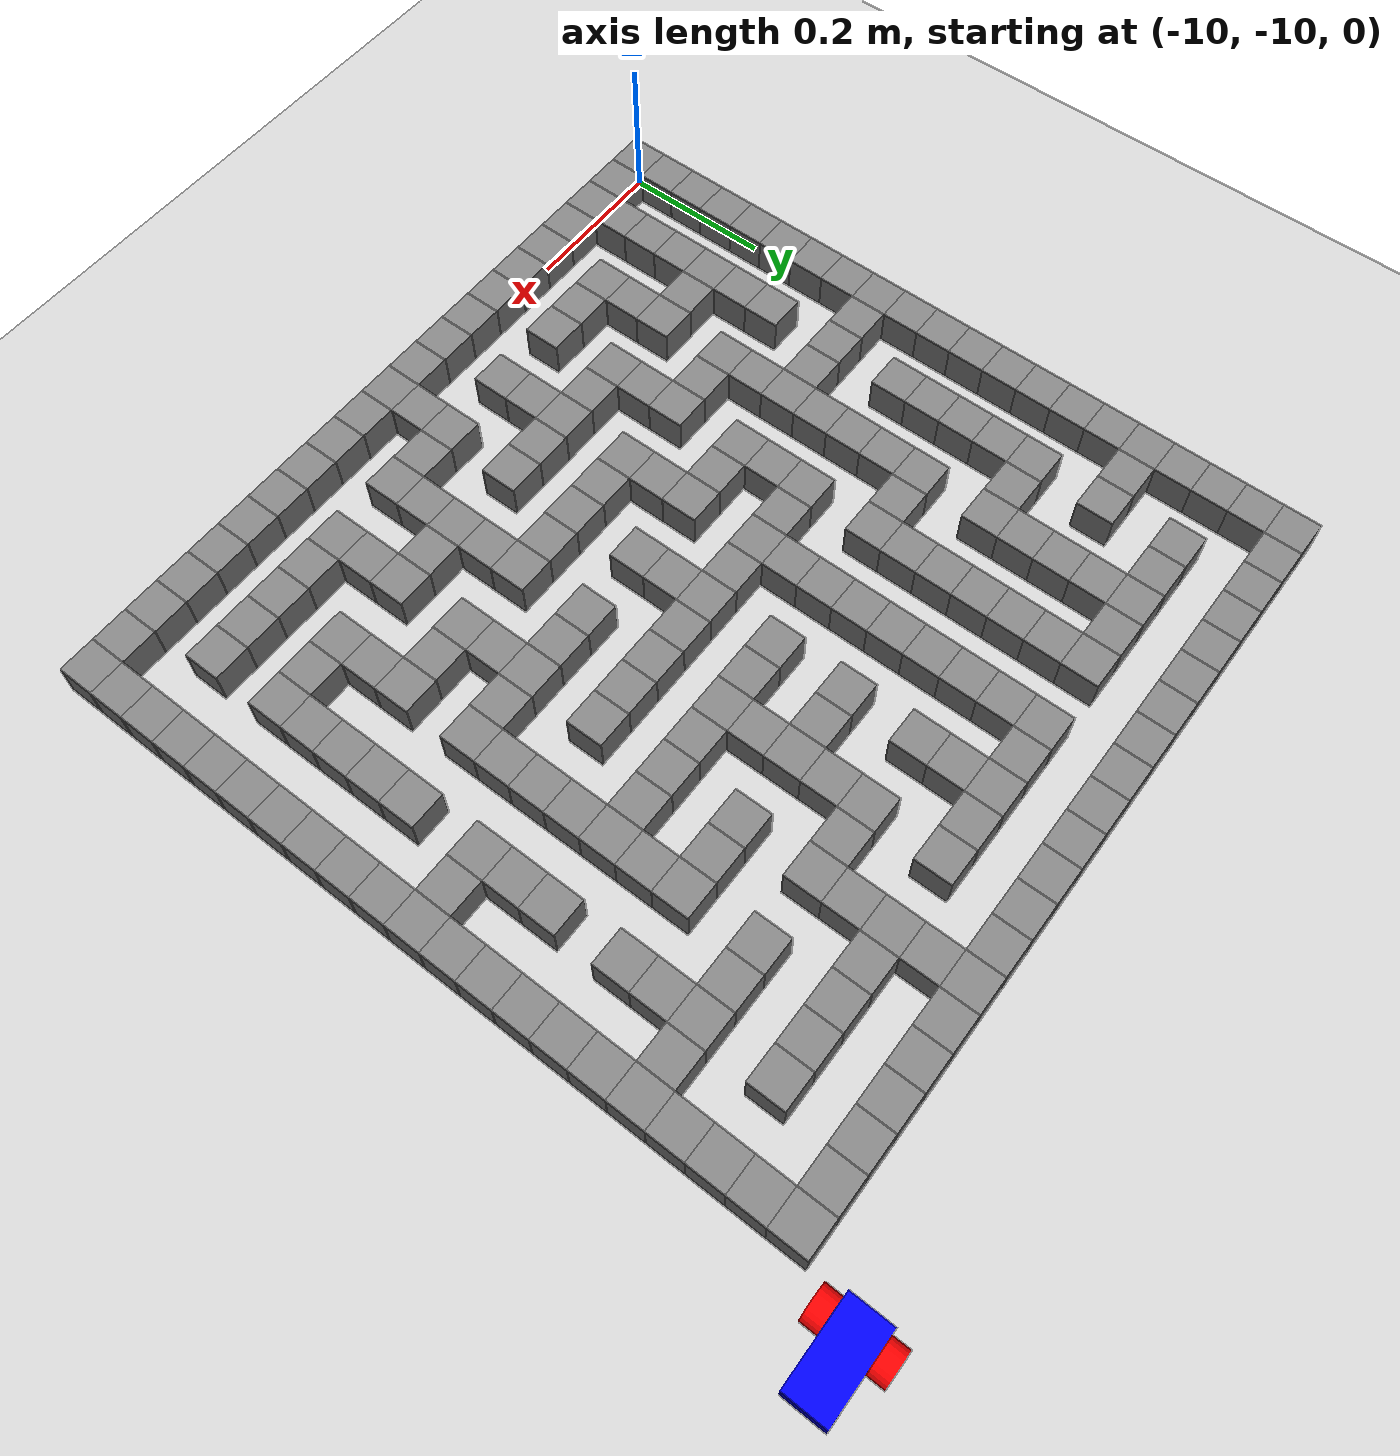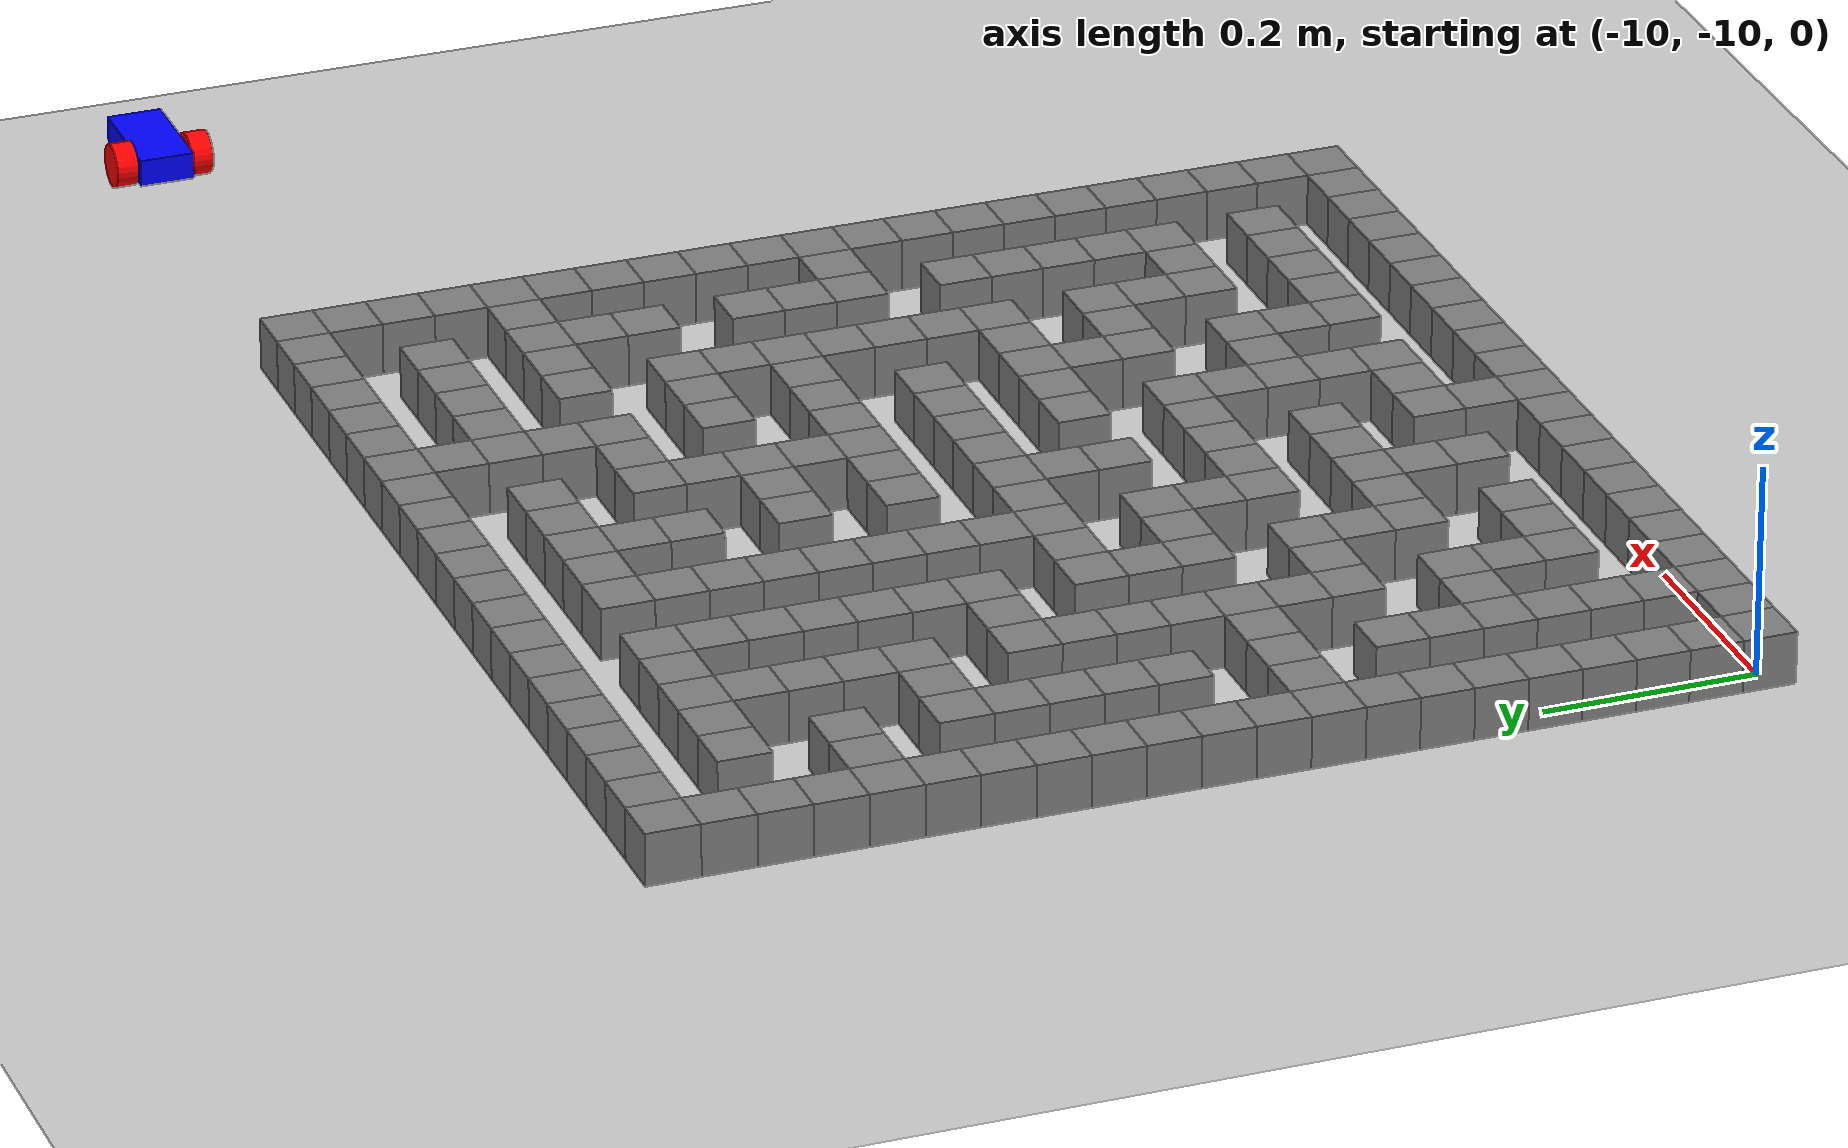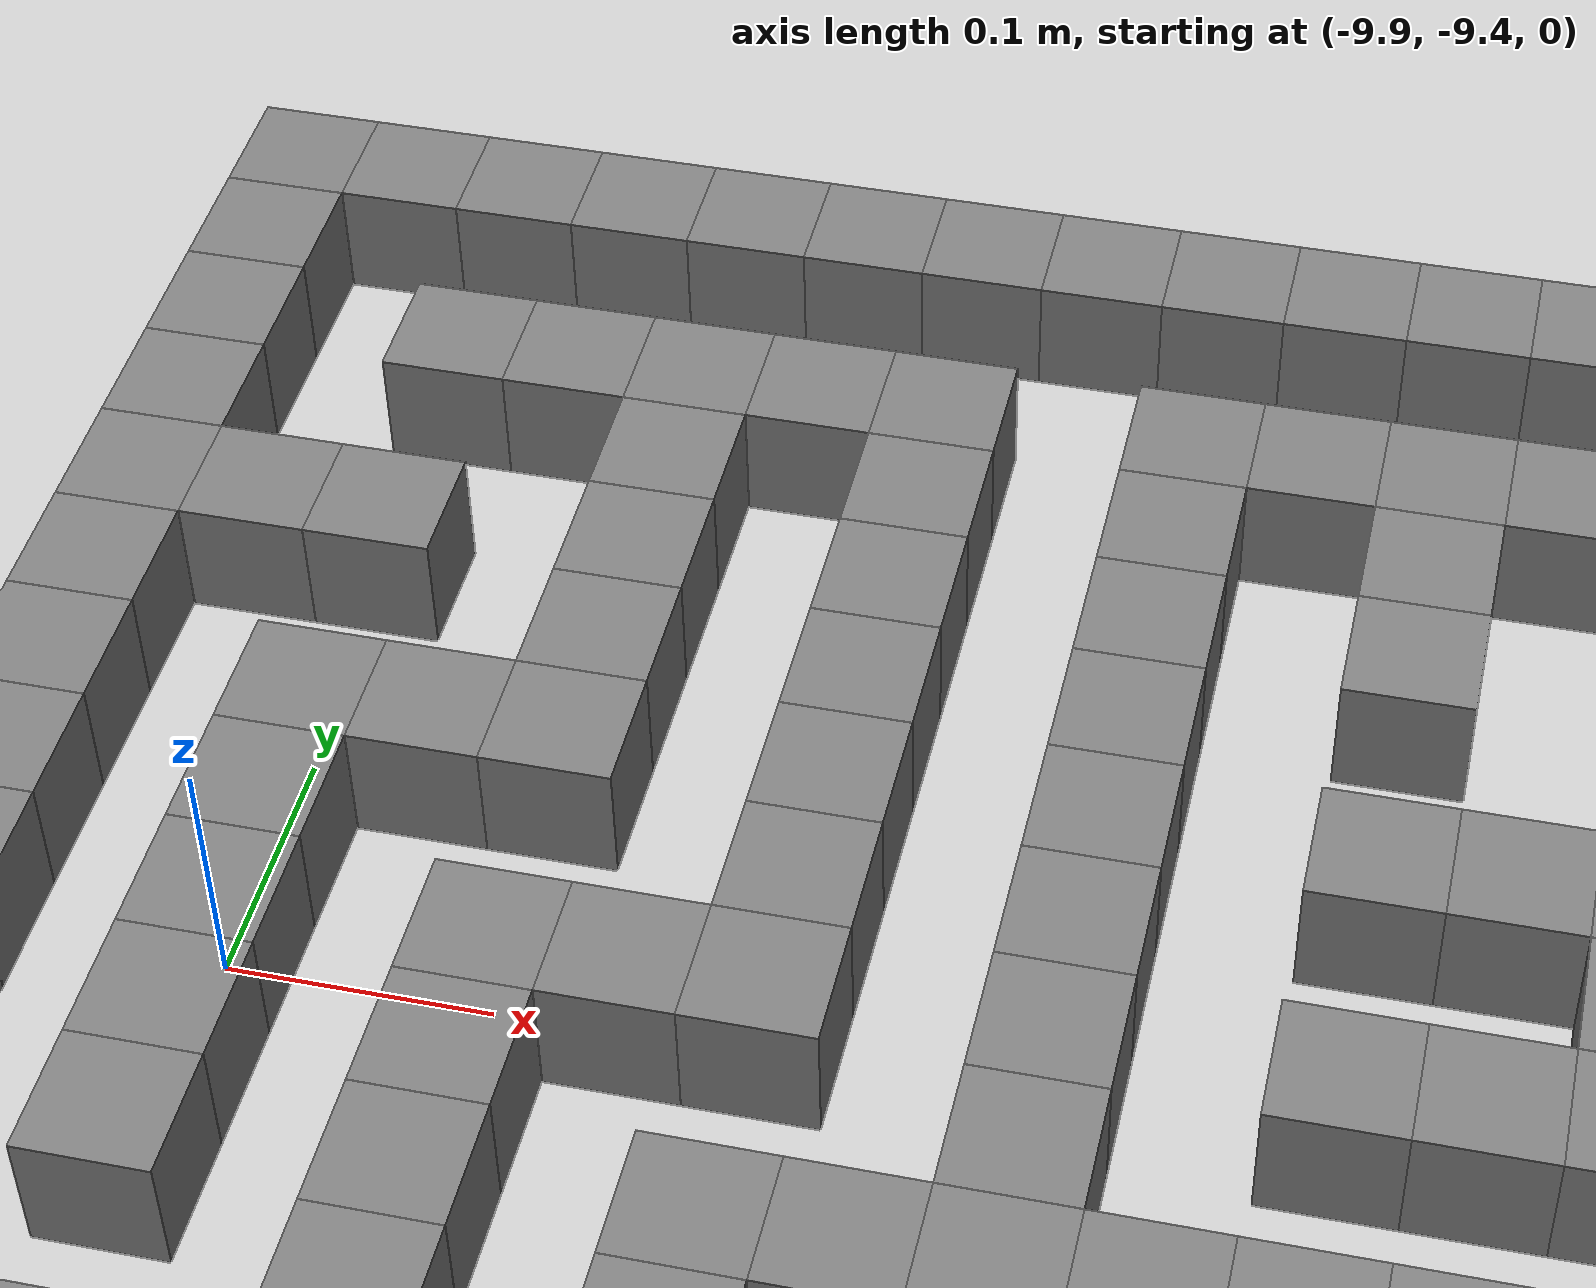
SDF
<?xml version="1.0" ?>
<sdf version="1.8">
    <world name="car_world">
        <include>
            <uri>file:///home/deyung/ros2_ws/src/myproject/maze_model.sdf</uri>
            <pose>-10 -10 0 0 0 0</pose> <!-- Maze at origin -->
        </include>
        <physics name="1ms" type="ignored">
            <max_step_size>0.001</max_step_size>
            <real_time_factor>1.0</real_time_factor>
        </physics>
        <!-- Moving Forward-->
        <plugin
            filename="gz-sim-triggered-publisher-system"
            name="gz::sim::systems::TriggeredPublisher">
            <input type="gz.msgs.Int32" topic="/keyboard/keypress">
            <match field="data">16777235</match>
            </input>
            <output type="gz.msgs.Twist" topic="/cmd_vel">
            linear: {x: 2}, angular: {z: 0.0}
            </output>
        </plugin>
        <!-- Moving Backward-->
        <plugin filename="gz-sim-triggered-publisher-system"
               name="gz::sim::systems::TriggeredPublisher">
           <input type="gz.msgs.Int32" topic="/keyboard/keypress">
               <match field="data">16777237</match>
           </input>
           <output type="gz.msgs.Twist" topic="/cmd_vel">
               linear: {x: -2}, angular: {z: 0.0}
           </output>
        </plugin>
        <!-- Left turn-->
         <plugin filename="gz-sim-triggered-publisher-system"
               name="gz::sim::systems::TriggeredPublisher">
           <input type="gz.msgs.Int32" topic="/keyboard/keypress">
               <match field="data">16777234</match>
           </input>
           <output type="gz.msgs.Twist" topic="/cmd_vel">
               linear: {x: 0.01}, angular: {z: 2}
           </output>
        </plugin>
        <!-- Right turn-->
         <plugin filename="gz-sim-triggered-publisher-system"
               name="gz::sim::systems::TriggeredPublisher">
           <input type="gz.msgs.Int32" topic="/keyboard/keypress">
               <match field="data">16777236</match>
           </input>
           <output type="gz.msgs.Twist" topic="/cmd_vel">
               linear: {x: 0.01}, angular: {z: -2}
           </output>
        </plugin>
        <plugin
            filename="gz-sim-sensors-system"
            name="gz::sim::systems::Sensors">
            <render_engine>ogre2</render_engine>
        </plugin>
        <plugin
            filename="gz-sim-physics-system"
            name="gz::sim::systems::Physics">
        </plugin>
        <plugin
            filename="gz-sim-user-commands-system"
            name="gz::sim::systems::UserCommands">
        </plugin>
        <plugin
            filename="gz-sim-scene-broadcaster-system"
            name="gz::sim::systems::SceneBroadcaster">
        </plugin>
        <plugin
            filename="gz-sim-imu-system"
            name="gz::sim::systems::Imu">
        </plugin>
        <plugin
            filename="gz-sim-contact-system"
            name="gz::sim::systems::Contact">
        </plugin>

        <light type="directional" name="sun">
            <cast_shadows>true</cast_shadows>
            <pose>0 0 10 0 0 0</pose>
            <diffuse>0.8 0.8 0.8 1</diffuse>
            <specular>0.2 0.2 0.2 1</specular>
            <attenuation>
                <range>1000</range>
                <constant>0.9</constant>
                <linear>0.01</linear>
                <quadratic>0.001</quadratic>
            </attenuation>
            <direction>-0.5 0.1 -0.9</direction>
        </light>

        <model name="ground_plane">
            <static>true</static>
            <link name="link">
                <collision name="collision">
                <geometry>
                    <plane>
                    <normal>0 0 1</normal>
                    </plane>
                </geometry>
                </collision>
                <visual name="visual">
                <geometry>
                    <plane>
                    <normal>0 0 1</normal>
                    <size>100 100</size>
                    </plane>
                </geometry>
                <material>
                    <ambient>0.8 0.8 0.8 1</ambient>
                    <diffuse>0.8 0.8 0.8 1</diffuse>
                    <specular>0.8 0.8 0.8 1</specular>
                </material>
                </visual>
            </link>
        </model>

        <model name='vehicle_blue' canonical_link='chassis'>

            <pose relative_to='world'>-8.9 -8.9 0.2 0 0 0</pose>   <!--the pose is relative to the start point of the maze-->
            <frame name="lidar_frame" attached_to='chassis'>
                    <pose>0.8 0 0.5 0 0 0</pose>
            </frame>
            <!--chassis-->
            <link name='chassis'>
                <pose relative_to='__model__'>0 0 0 0 0 0</pose>

                <inertial> <!--inertial properties of the link mass, inertia matix density is 1.14395
                all numbers is in SI unit-->
                    <mass>0.000143</mass>
                    <inertia>
                        <ixx>0.000000447</ixx>
                        <ixy>0</ixy>
                        <ixz>0</ixz>
                        <iyy>0.00000152</iyy>
                        <iyz>0</iyz>
                        <izz>0.00000179</izz>
                    </inertia>
                </inertial>
                <visual name='visual'>
                    <geometry>
                        <box>
                            <size>0.1 0.05 0.025</size>
                        </box>
                    </geometry>
                    <!--Color of the link -->
                    <material>
                        <ambient>0.0 0.0 1.0 1</ambient>
                        <diffuse>0.0 0.0 1.0 1</diffuse>
                        <specular>0.0 0.0 1.0 1</specular>
                    </material>
                </visual>
                <collision name='collision'>
                    <geometry>
                        <box>
                           <size>0.1 0.05 0.025</size>
                        </box>
                    </geometry>
                </collision>
                <sensor name="imu_sensor" type="imu">
                    <always_on>1</always_on>
                    <update_rate>1</update_rate>
                    <visualize>true</visualize>
                    <topic>imu</topic>
                </sensor>

                <sensor name='gpu_lidar' type='gpu_lidar'>"
                    <pose relative_to='lidar_frame'>0 0 0 0 0 0</pose>
                    <topic>lidar</topic>
                    <update_rate>10</update_rate>
                    <ray>
                        <scan>
                            <horizontal>
                                <samples>640</samples>
                                <resolution>1</resolution>
                                <min_angle>-1.396263</min_angle>
                                <max_angle>1.396263</max_angle>
                            </horizontal>
                            <vertical>
                                <samples>1</samples>
                                <resolution>0.01</resolution>
                                <min_angle>0</min_angle>
                                <max_angle>0</max_angle>
                            </vertical>
                        </scan>
                        <range>
                            <min>0.08</min>
                            <max>10.0</max>
                            <resolution>0.01</resolution>
                        </range>
                    </ray>
                    <always_on>1</always_on>
                    <visualize>true</visualize>
                </sensor>
                <!-- Contact (bumper) sensor -->
                <sensor name="bumper_contacts" type="contact">
                      <update_rate>50</update_rate>
                      <!-- Monitor this/these collision(s) for contacts -->
                      <contact>
                        <collision>collision</collision>
                      </contact>
                      <!-- Gazebo Transport topic name -->
                      <topic>contacts</topic>
                      <always_on>true</always_on>
                      <visualize>false</visualize>
                </sensor>
            </link>

            <!--Left wheel-->
            <link name='left_wheel'>
                <pose relative_to="chassis">-0.025 0.035 0 -1.5707 0 0</pose> <!--angles are in radian-->
                <inertial>
                    <mass>0.25</mass>
                    <inertia>
                        <ixx>0.000033333</ixx>
                        <ixy>0</ixy>
                        <ixz>0</ixz>
                        <iyy>0.000033333</iyy>
                        <iyz>0</iyz>
                        <izz>0.00005</izz>
                    </inertia>
                </inertial>
                <visual name='visual'>
                    <geometry>
                        <cylinder>
                            <radius>0.02</radius>
                            <length>0.02</length>
                        </cylinder>
                    </geometry>
                    <material>
                        <ambient>1.0 0.0 0.0 1</ambient>
                        <diffuse>1.0 0.0 0.0 1</diffuse>
                        <specular>1.0 0.0 0.0 1</specular>
                    </material>
                </visual>
                <collision name='collision'>
                    <geometry>
                        <cylinder>
                            <radius>0.02</radius>
                            <length>0.02</length>
                        </cylinder>
                    </geometry>
                </collision>
            </link>

            <!--The same as left wheel but with different position-->
            <link name='right_wheel'>
                <pose relative_to="chassis">-0.025 -0.035 0 -1.5707 0 0</pose> <!--angles are in radian-->
                <inertial>
                    <mass>0.25</mass>
                    <inertia>
                        <ixx>0.000033333</ixx>
                        <ixy>0</ixy>
                        <ixz>0</ixz>
                        <iyy>0.000033333</iyy>
                        <iyz>0</iyz>
                        <izz>0.00005</izz>
                    </inertia>
                </inertial>
                <visual name='visual'>
                    <geometry>
                        <cylinder>
                            <radius>0.02</radius>
                            <length>0.02</length>
                        </cylinder>
                    </geometry>
                    <material>
                        <ambient>1.0 0.0 0.0 1</ambient>
                        <diffuse>1.0 0.0 0.0 1</diffuse>
                        <specular>1.0 0.0 0.0 1</specular>
                    </material>
                </visual>
                <collision name='collision'>
                    <geometry>
                        <cylinder>
                            <radius>0.02</radius>
                            <length>0.02</length>
                        </cylinder>
                    </geometry>
                </collision>
            </link>

            <!--arbitrary frame-->
            <frame name="caster_frame" attached_to='chassis'>
                <pose>0.04 0 -0.01 0 0 0</pose>
            </frame>

            <!--caster wheel-->
            <link name='caster'>
                <pose relative_to='caster_frame'/>
                <inertial>
                    <mass>0.125</mass>
                    <inertia>
                        <ixx>0.000005</ixx>
                        <ixy>0</ixy>
                        <ixz>0</ixz>
                        <iyy>0.000005</iyy>
                        <iyz>0</iyz>
                        <izz>0.000005</izz>
                    </inertia>
                </inertial>
                <visual name='visual'>
                    <geometry>
                        <sphere>
                            <radius>0.01</radius>
                        </sphere>
                    </geometry>
                    <material>
                        <ambient>0.0 1 0.0 1</ambient>
                        <diffuse>0.0 1 0.0 1</diffuse>
                        <specular>0.0 1 0.0 1</specular>
                    </material>
                </visual>
                <collision name='collision'>
                    <geometry>
                        <sphere>
                            <radius>0.01</radius>
                        </sphere>
                    </geometry>
                </collision>
            </link>

            <!--left wheel joint-->
            <joint name='left_wheel_joint' type='revolute'>
                <pose relative_to='left_wheel'/>
                <parent>chassis</parent>
                <child>left_wheel</child>
                <axis>
                    <xyz expressed_in='__model__'>0 1 0</xyz> <!--can be descired to any frame or even arbitrary frames-->
                    <limit>
                        <lower>-1.79769e+308</lower>    <!--negative infinity-->
                        <upper>1.79769e+308</upper>     <!--positive infinity-->
                    </limit>
                </axis>
            </joint>

            <!--right wheel joint-->
            <joint name='right_wheel_joint' type='revolute'>
                <pose relative_to='right_wheel'/>
                <parent>chassis</parent>
                <child>right_wheel</child>
                <axis>
                    <xyz expressed_in='__model__'>0 1 0</xyz>
                    <limit>
                        <lower>-1.79769e+308</lower>    <!--negative infinity-->
                        <upper>1.79769e+308</upper>     <!--positive infinity-->
                    </limit>
                </axis>
            </joint>

            <!--caster wheel joint--> <!--pose defult value is the child-->
            <joint name='caster_wheel' type='ball'>
                <parent>chassis</parent>
                <child>caster</child>
            </joint>

            <plugin
                filename="gz-sim-diff-drive-system"
                name="gz::sim::systems::DiffDrive">
                <left_joint>left_wheel_joint</left_joint>
                <right_joint>right_wheel_joint</right_joint>
                <wheel_separation>1.2</wheel_separation>
                <wheel_radius>0.4</wheel_radius>
                <odom_publish_frequency>1</odom_publish_frequency>
                <topic>cmd_vel</topic>
                <odometry_topic>odom</odometry_topic>
            </plugin>
        </model>

    </world>
</sdf>

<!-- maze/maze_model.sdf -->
<sdf version="1.9">
  <model name="maze">
    <static>true</static>

    <link name="wall_0_0">
      <pose>0.0 0.0 0.025 0 0 0</pose>
      <collision name="collision">
        <geometry>
          <box><size>0.05 0.05 0.05</size></box>
        </geometry>
      </collision>
      <visual name="visual">
        <geometry>
          <box><size>0.05 0.05 0.05</size></box>
        </geometry>
        <material><ambient>0.5 0.5 0.5 1</ambient></material>
      </visual>
    </link>

    <link name="wall_0_1">
      <pose>0.0 0.05 0.025 0 0 0</pose>
      <collision name="collision">
        <geometry>
          <box><size>0.05 0.05 0.05</size></box>
        </geometry>
      </collision>
      <visual name="visual">
        <geometry>
          <box><size>0.05 0.05 0.05</size></box>
        </geometry>
        <material><ambient>0.5 0.5 0.5 1</ambient></material>
      </visual>
    </link>

    <link name="wall_0_2">
      <pose>0.0 0.1 0.025 0 0 0</pose>
      <collision name="collision">
        <geometry>
          <box><size>0.05 0.05 0.05</size></box>
        </geometry>
      </collision>
      <visual name="visual">
        <geometry>
          <box><size>0.05 0.05 0.05</size></box>
        </geometry>
        <material><ambient>0.5 0.5 0.5 1</ambient></material>
      </visual>
    </link>

    <link name="wall_0_3">
      <pose>0.0 0.15000000000000002 0.025 0 0 0</pose>
      <collision name="collision">
        <geometry>
          <box><size>0.05 0.05 0.05</size></box>
        </geometry>
      </collision>
      <visual name="visual">
        <geometry>
          <box><size>0.05 0.05 0.05</size></box>
        </geometry>
        <material><ambient>0.5 0.5 0.5 1</ambient></material>
      </visual>
    </link>

    <link name="wall_0_4">
      <pose>0.0 0.2 0.025 0 0 0</pose>
      <collision name="collision">
        <geometry>
          <box><size>0.05 0.05 0.05</size></box>
        </geometry>
      </collision>
      <visual name="visual">
        <geometry>
          <box><size>0.05 0.05 0.05</size></box>
        </geometry>
        <material><ambient>0.5 0.5 0.5 1</ambient></material>
      </visual>
    </link>

    <link name="wall_0_5">
      <pose>0.0 0.25 0.025 0 0 0</pose>
      <collision name="collision">
        <geometry>
          <box><size>0.05 0.05 0.05</size></box>
        </geometry>
      </collision>
      <visual name="visual">
        <geometry>
          <box><size>0.05 0.05 0.05</size></box>
        </geometry>
        <material><ambient>0.5 0.5 0.5 1</ambient></material>
      </visual>
    </link>

    <link name="wall_0_6">
      <pose>0.0 0.30000000000000004 0.025 0 0 0</pose>
      <collision name="collision">
        <geometry>
          <box><size>0.05 0.05 0.05</size></box>
        </geometry>
      </collision>
      <visual name="visual">
        <geometry>
          <box><size>0.05 0.05 0.05</size></box>
        </geometry>
        <material><ambient>0.5 0.5 0.5 1</ambient></material>
      </visual>
    </link>

    <link name="wall_0_7">
      <pose>0.0 0.35000000000000003 0.025 0 0 0</pose>
      <collision name="collision">
        <geometry>
          <box><size>0.05 0.05 0.05</size></box>
        </geometry>
      </collision>
      <visual name="visual">
        <geometry>
          <box><size>0.05 0.05 0.05</size></box>
        </geometry>
        <material><ambient>0.5 0.5 0.5 1</ambient></material>
      </visual>
    </link>

    <link name="wall_0_8">
      <pose>0.0 0.4 0.025 0 0 0</pose>
      <collision name="collision">
        <geometry>
          <box><size>0.05 0.05 0.05</size></box>
        </geometry>
      </collision>
      <visual name="visual">
        <geometry>
          <box><size>0.05 0.05 0.05</size></box>
        </geometry>
        <material><ambient>0.5 0.5 0.5 1</ambient></material>
      </visual>
    </link>

    <link name="wall_0_9">
      <pose>0.0 0.45 0.025 0 0 0</pose>
      <collision name="collision">
        <geometry>
          <box><size>0.05 0.05 0.05</size></box>
        </geometry>
      </collision>
      <visual name="visual">
        <geometry>
          <box><size>0.05 0.05 0.05</size></box>
        </geometry>
        <material><ambient>0.5 0.5 0.5 1</ambient></material>
      </visual>
    </link>

    <link name="wall_0_10">
      <pose>0.0 0.5 0.025 0 0 0</pose>
      <collision name="collision">
        <geometry>
          <box><size>0.05 0.05 0.05</size></box>
        </geometry>
      </collision>
      <visual name="visual">
        <geometry>
          <box><size>0.05 0.05 0.05</size></box>
        </geometry>
        <material><ambient>0.5 0.5 0.5 1</ambient></material>
      </visual>
    </link>

    <link name="wall_0_11">
      <pose>0.0 0.55 0.025 0 0 0</pose>
      <collision name="collision">
        <geometry>
          <box><size>0.05 0.05 0.05</size></box>
        </geometry>
      </collision>
      <visual name="visual">
        <geometry>
          <box><size>0.05 0.05 0.05</size></box>
        </geometry>
        <material><ambient>0.5 0.5 0.5 1</ambient></material>
      </visual>
    </link>

    <link name="wall_0_12">
      <pose>0.0 0.6000000000000001 0.025 0 0 0</pose>
      <collision name="collision">
        <geometry>
          <box><size>0.05 0.05 0.05</size></box>
        </geometry>
      </collision>
      <visual name="visual">
        <geometry>
          <box><size>0.05 0.05 0.05</size></box>
        </geometry>
        <material><ambient>0.5 0.5 0.5 1</ambient></material>
      </visual>
    </link>

    <link name="wall_0_13">
      <pose>0.0 0.65 0.025 0 0 0</pose>
      <collision name="collision">
        <geometry>
          <box><size>0.05 0.05 0.05</size></box>
        </geometry>
      </collision>
      <visual name="visual">
        <geometry>
          <box><size>0.05 0.05 0.05</size></box>
        </geometry>
        <material><ambient>0.5 0.5 0.5 1</ambient></material>
      </visual>
    </link>

    <link name="wall_0_14">
      <pose>0.0 0.7000000000000001 0.025 0 0 0</pose>
      <collision name="collision">
        <geometry>
          <box><size>0.05 0.05 0.05</size></box>
        </geometry>
      </collision>
      <visual name="visual">
        <geometry>
          <box><size>0.05 0.05 0.05</size></box>
        </geometry>
        <material><ambient>0.5 0.5 0.5 1</ambient></material>
      </visual>
    </link>

    <link name="wall_0_15">
      <pose>0.0 0.75 0.025 0 0 0</pose>
      <collision name="collision">
        <geometry>
          <box><size>0.05 0.05 0.05</size></box>
        </geometry>
      </collision>
      <visual name="visual">
        <geometry>
          <box><size>0.05 0.05 0.05</size></box>
        </geometry>
        <material><ambient>0.5 0.5 0.5 1</ambient></material>
      </visual>
    </link>

    <link name="wall_0_16">
      <pose>0.0 0.8 0.025 0 0 0</pose>
      <collision name="collision">
        <geometry>
          <box><size>0.05 0.05 0.05</size></box>
        </geometry>
      </collision>
      <visual name="visual">
        <geometry>
          <box><size>0.05 0.05 0.05</size></box>
        </geometry>
        <material><ambient>0.5 0.5 0.5 1</ambient></material>
      </visual>
    </link>

    <link name="wall_0_17">
      <pose>0.0 0.8500000000000001 0.025 0 0 0</pose>
      <collision name="collision">
        <geometry>
          <box><size>0.05 0.05 0.05</size></box>
        </geometry>
      </collision>
      <visual name="visual">
        <geometry>
          <box><size>0.05 0.05 0.05</size></box>
        </geometry>
        <material><ambient>0.5 0.5 0.5 1</ambient></material>
      </visual>
    </link>

    <link name="wall_0_18">
      <pose>0.0 0.9 0.025 0 0 0</pose>
      <collision name="collision">
        <geometry>
          <box><size>0.05 0.05 0.05</size></box>
        </geometry>
      </collision>
      <visual name="visual">
        <geometry>
          <box><size>0.05 0.05 0.05</size></box>
        </geometry>
        <material><ambient>0.5 0.5 0.5 1</ambient></material>
      </visual>
    </link>

    <link name="wall_0_19">
      <pose>0.0 0.9500000000000001 0.025 0 0 0</pose>
      <collision name="collision">
        <geometry>
          <box><size>0.05 0.05 0.05</size></box>
        </geometry>
      </collision>
      <visual name="visual">
        <geometry>
          <box><size>0.05 0.05 0.05</size></box>
        </geometry>
        <material><ambient>0.5 0.5 0.5 1</ambient></material>
      </visual>
    </link>

    <link name="wall_0_20">
      <pose>0.0 1.0 0.025 0 0 0</pose>
      <collision name="collision">
        <geometry>
          <box><size>0.05 0.05 0.05</size></box>
        </geometry>
      </collision>
      <visual name="visual">
        <geometry>
          <box><size>0.05 0.05 0.05</size></box>
        </geometry>
        <material><ambient>0.5 0.5 0.5 1</ambient></material>
      </visual>
    </link>

    <link name="wall_1_0">
      <pose>0.05 0.0 0.025 0 0 0</pose>
      <collision name="collision">
        <geometry>
          <box><size>0.05 0.05 0.05</size></box>
        </geometry>
      </collision>
      <visual name="visual">
        <geometry>
          <box><size>0.05 0.05 0.05</size></box>
        </geometry>
        <material><ambient>0.5 0.5 0.5 1</ambient></material>
      </visual>
    </link>

    <link name="wall_1_8">
      <pose>0.05 0.4 0.025 0 0 0</pose>
      <collision name="collision">
        <geometry>
          <box><size>0.05 0.05 0.05</size></box>
        </geometry>
      </collision>
      <visual name="visual">
        <geometry>
          <box><size>0.05 0.05 0.05</size></box>
        </geometry>
        <material><ambient>0.5 0.5 0.5 1</ambient></material>
      </visual>
    </link>

    <link name="wall_1_16">
      <pose>0.05 0.8 0.025 0 0 0</pose>
      <collision name="collision">
        <geometry>
          <box><size>0.05 0.05 0.05</size></box>
        </geometry>
      </collision>
      <visual name="visual">
        <geometry>
          <box><size>0.05 0.05 0.05</size></box>
        </geometry>
        <material><ambient>0.5 0.5 0.5 1</ambient></material>
      </visual>
    </link>

    <link name="wall_1_20">
      <pose>0.05 1.0 0.025 0 0 0</pose>
      <collision name="collision">
        <geometry>
          <box><size>0.05 0.05 0.05</size></box>
        </geometry>
      </collision>
      <visual name="visual">
        <geometry>
          <box><size>0.05 0.05 0.05</size></box>
        </geometry>
        <material><ambient>0.5 0.5 0.5 1</ambient></material>
      </visual>
    </link>

    <link name="wall_2_0">
      <pose>0.1 0.0 0.025 0 0 0</pose>
      <collision name="collision">
        <geometry>
          <box><size>0.05 0.05 0.05</size></box>
        </geometry>
      </collision>
      <visual name="visual">
        <geometry>
          <box><size>0.05 0.05 0.05</size></box>
        </geometry>
        <material><ambient>0.5 0.5 0.5 1</ambient></material>
      </visual>
    </link>

    <link name="wall_2_1">
      <pose>0.1 0.05 0.025 0 0 0</pose>
      <collision name="collision">
        <geometry>
          <box><size>0.05 0.05 0.05</size></box>
        </geometry>
      </collision>
      <visual name="visual">
        <geometry>
          <box><size>0.05 0.05 0.05</size></box>
        </geometry>
        <material><ambient>0.5 0.5 0.5 1</ambient></material>
      </visual>
    </link>

    <link name="wall_2_2">
      <pose>0.1 0.1 0.025 0 0 0</pose>
      <collision name="collision">
        <geometry>
          <box><size>0.05 0.05 0.05</size></box>
        </geometry>
      </collision>
      <visual name="visual">
        <geometry>
          <box><size>0.05 0.05 0.05</size></box>
        </geometry>
        <material><ambient>0.5 0.5 0.5 1</ambient></material>
      </visual>
    </link>

    <link name="wall_2_3">
      <pose>0.1 0.15000000000000002 0.025 0 0 0</pose>
      <collision name="collision">
        <geometry>
          <box><size>0.05 0.05 0.05</size></box>
        </geometry>
      </collision>
      <visual name="visual">
        <geometry>
          <box><size>0.05 0.05 0.05</size></box>
        </geometry>
        <material><ambient>0.5 0.5 0.5 1</ambient></material>
      </visual>
    </link>

    <link name="wall_2_4">
      <pose>0.1 0.2 0.025 0 0 0</pose>
      <collision name="collision">
        <geometry>
          <box><size>0.05 0.05 0.05</size></box>
        </geometry>
      </collision>
      <visual name="visual">
        <geometry>
          <box><size>0.05 0.05 0.05</size></box>
        </geometry>
        <material><ambient>0.5 0.5 0.5 1</ambient></material>
      </visual>
    </link>

    <link name="wall_2_5">
      <pose>0.1 0.25 0.025 0 0 0</pose>
      <collision name="collision">
        <geometry>
          <box><size>0.05 0.05 0.05</size></box>
        </geometry>
      </collision>
      <visual name="visual">
        <geometry>
          <box><size>0.05 0.05 0.05</size></box>
        </geometry>
        <material><ambient>0.5 0.5 0.5 1</ambient></material>
      </visual>
    </link>

    <link name="wall_2_6">
      <pose>0.1 0.30000000000000004 0.025 0 0 0</pose>
      <collision name="collision">
        <geometry>
          <box><size>0.05 0.05 0.05</size></box>
        </geometry>
      </collision>
      <visual name="visual">
        <geometry>
          <box><size>0.05 0.05 0.05</size></box>
        </geometry>
        <material><ambient>0.5 0.5 0.5 1</ambient></material>
      </visual>
    </link>

    <link name="wall_2_8">
      <pose>0.1 0.4 0.025 0 0 0</pose>
      <collision name="collision">
        <geometry>
          <box><size>0.05 0.05 0.05</size></box>
        </geometry>
      </collision>
      <visual name="visual">
        <geometry>
          <box><size>0.05 0.05 0.05</size></box>
        </geometry>
        <material><ambient>0.5 0.5 0.5 1</ambient></material>
      </visual>
    </link>

    <link name="wall_2_10">
      <pose>0.1 0.5 0.025 0 0 0</pose>
      <collision name="collision">
        <geometry>
          <box><size>0.05 0.05 0.05</size></box>
        </geometry>
      </collision>
      <visual name="visual">
        <geometry>
          <box><size>0.05 0.05 0.05</size></box>
        </geometry>
        <material><ambient>0.5 0.5 0.5 1</ambient></material>
      </visual>
    </link>

    <link name="wall_2_11">
      <pose>0.1 0.55 0.025 0 0 0</pose>
      <collision name="collision">
        <geometry>
          <box><size>0.05 0.05 0.05</size></box>
        </geometry>
      </collision>
      <visual name="visual">
        <geometry>
          <box><size>0.05 0.05 0.05</size></box>
        </geometry>
        <material><ambient>0.5 0.5 0.5 1</ambient></material>
      </visual>
    </link>

    <link name="wall_2_12">
      <pose>0.1 0.6000000000000001 0.025 0 0 0</pose>
      <collision name="collision">
        <geometry>
          <box><size>0.05 0.05 0.05</size></box>
        </geometry>
      </collision>
      <visual name="visual">
        <geometry>
          <box><size>0.05 0.05 0.05</size></box>
        </geometry>
        <material><ambient>0.5 0.5 0.5 1</ambient></material>
      </visual>
    </link>

    <link name="wall_2_13">
      <pose>0.1 0.65 0.025 0 0 0</pose>
      <collision name="collision">
        <geometry>
          <box><size>0.05 0.05 0.05</size></box>
        </geometry>
      </collision>
      <visual name="visual">
        <geometry>
          <box><size>0.05 0.05 0.05</size></box>
        </geometry>
        <material><ambient>0.5 0.5 0.5 1</ambient></material>
      </visual>
    </link>

    <link name="wall_2_14">
      <pose>0.1 0.7000000000000001 0.025 0 0 0</pose>
      <collision name="collision">
        <geometry>
          <box><size>0.05 0.05 0.05</size></box>
        </geometry>
      </collision>
      <visual name="visual">
        <geometry>
          <box><size>0.05 0.05 0.05</size></box>
        </geometry>
        <material><ambient>0.5 0.5 0.5 1</ambient></material>
      </visual>
    </link>

    <link name="wall_2_16">
      <pose>0.1 0.8 0.025 0 0 0</pose>
      <collision name="collision">
        <geometry>
          <box><size>0.05 0.05 0.05</size></box>
        </geometry>
      </collision>
      <visual name="visual">
        <geometry>
          <box><size>0.05 0.05 0.05</size></box>
        </geometry>
        <material><ambient>0.5 0.5 0.5 1</ambient></material>
      </visual>
    </link>

    <link name="wall_2_18">
      <pose>0.1 0.9 0.025 0 0 0</pose>
      <collision name="collision">
        <geometry>
          <box><size>0.05 0.05 0.05</size></box>
        </geometry>
      </collision>
      <visual name="visual">
        <geometry>
          <box><size>0.05 0.05 0.05</size></box>
        </geometry>
        <material><ambient>0.5 0.5 0.5 1</ambient></material>
      </visual>
    </link>

    <link name="wall_2_20">
      <pose>0.1 1.0 0.025 0 0 0</pose>
      <collision name="collision">
        <geometry>
          <box><size>0.05 0.05 0.05</size></box>
        </geometry>
      </collision>
      <visual name="visual">
        <geometry>
          <box><size>0.05 0.05 0.05</size></box>
        </geometry>
        <material><ambient>0.5 0.5 0.5 1</ambient></material>
      </visual>
    </link>

    <link name="wall_3_0">
      <pose>0.15000000000000002 0.0 0.025 0 0 0</pose>
      <collision name="collision">
        <geometry>
          <box><size>0.05 0.05 0.05</size></box>
        </geometry>
      </collision>
      <visual name="visual">
        <geometry>
          <box><size>0.05 0.05 0.05</size></box>
        </geometry>
        <material><ambient>0.5 0.5 0.5 1</ambient></material>
      </visual>
    </link>

    <link name="wall_3_4">
      <pose>0.15000000000000002 0.2 0.025 0 0 0</pose>
      <collision name="collision">
        <geometry>
          <box><size>0.05 0.05 0.05</size></box>
        </geometry>
      </collision>
      <visual name="visual">
        <geometry>
          <box><size>0.05 0.05 0.05</size></box>
        </geometry>
        <material><ambient>0.5 0.5 0.5 1</ambient></material>
      </visual>
    </link>

    <link name="wall_3_8">
      <pose>0.15000000000000002 0.4 0.025 0 0 0</pose>
      <collision name="collision">
        <geometry>
          <box><size>0.05 0.05 0.05</size></box>
        </geometry>
      </collision>
      <visual name="visual">
        <geometry>
          <box><size>0.05 0.05 0.05</size></box>
        </geometry>
        <material><ambient>0.5 0.5 0.5 1</ambient></material>
      </visual>
    </link>

    <link name="wall_3_14">
      <pose>0.15000000000000002 0.7000000000000001 0.025 0 0 0</pose>
      <collision name="collision">
        <geometry>
          <box><size>0.05 0.05 0.05</size></box>
        </geometry>
      </collision>
      <visual name="visual">
        <geometry>
          <box><size>0.05 0.05 0.05</size></box>
        </geometry>
        <material><ambient>0.5 0.5 0.5 1</ambient></material>
      </visual>
    </link>

    <link name="wall_3_18">
      <pose>0.15000000000000002 0.9 0.025 0 0 0</pose>
      <collision name="collision">
        <geometry>
          <box><size>0.05 0.05 0.05</size></box>
        </geometry>
      </collision>
      <visual name="visual">
        <geometry>
          <box><size>0.05 0.05 0.05</size></box>
        </geometry>
        <material><ambient>0.5 0.5 0.5 1</ambient></material>
      </visual>
    </link>

    <link name="wall_3_20">
      <pose>0.15000000000000002 1.0 0.025 0 0 0</pose>
      <collision name="collision">
        <geometry>
          <box><size>0.05 0.05 0.05</size></box>
        </geometry>
      </collision>
      <visual name="visual">
        <geometry>
          <box><size>0.05 0.05 0.05</size></box>
        </geometry>
        <material><ambient>0.5 0.5 0.5 1</ambient></material>
      </visual>
    </link>

    <link name="wall_4_0">
      <pose>0.2 0.0 0.025 0 0 0</pose>
      <collision name="collision">
        <geometry>
          <box><size>0.05 0.05 0.05</size></box>
        </geometry>
      </collision>
      <visual name="visual">
        <geometry>
          <box><size>0.05 0.05 0.05</size></box>
        </geometry>
        <material><ambient>0.5 0.5 0.5 1</ambient></material>
      </visual>
    </link>

    <link name="wall_4_2">
      <pose>0.2 0.1 0.025 0 0 0</pose>
      <collision name="collision">
        <geometry>
          <box><size>0.05 0.05 0.05</size></box>
        </geometry>
      </collision>
      <visual name="visual">
        <geometry>
          <box><size>0.05 0.05 0.05</size></box>
        </geometry>
        <material><ambient>0.5 0.5 0.5 1</ambient></material>
      </visual>
    </link>

    <link name="wall_4_3">
      <pose>0.2 0.15000000000000002 0.025 0 0 0</pose>
      <collision name="collision">
        <geometry>
          <box><size>0.05 0.05 0.05</size></box>
        </geometry>
      </collision>
      <visual name="visual">
        <geometry>
          <box><size>0.05 0.05 0.05</size></box>
        </geometry>
        <material><ambient>0.5 0.5 0.5 1</ambient></material>
      </visual>
    </link>

    <link name="wall_4_4">
      <pose>0.2 0.2 0.025 0 0 0</pose>
      <collision name="collision">
        <geometry>
          <box><size>0.05 0.05 0.05</size></box>
        </geometry>
      </collision>
      <visual name="visual">
        <geometry>
          <box><size>0.05 0.05 0.05</size></box>
        </geometry>
        <material><ambient>0.5 0.5 0.5 1</ambient></material>
      </visual>
    </link>

    <link name="wall_4_6">
      <pose>0.2 0.30000000000000004 0.025 0 0 0</pose>
      <collision name="collision">
        <geometry>
          <box><size>0.05 0.05 0.05</size></box>
        </geometry>
      </collision>
      <visual name="visual">
        <geometry>
          <box><size>0.05 0.05 0.05</size></box>
        </geometry>
        <material><ambient>0.5 0.5 0.5 1</ambient></material>
      </visual>
    </link>

    <link name="wall_4_7">
      <pose>0.2 0.35000000000000003 0.025 0 0 0</pose>
      <collision name="collision">
        <geometry>
          <box><size>0.05 0.05 0.05</size></box>
        </geometry>
      </collision>
      <visual name="visual">
        <geometry>
          <box><size>0.05 0.05 0.05</size></box>
        </geometry>
        <material><ambient>0.5 0.5 0.5 1</ambient></material>
      </visual>
    </link>

    <link name="wall_4_8">
      <pose>0.2 0.4 0.025 0 0 0</pose>
      <collision name="collision">
        <geometry>
          <box><size>0.05 0.05 0.05</size></box>
        </geometry>
      </collision>
      <visual name="visual">
        <geometry>
          <box><size>0.05 0.05 0.05</size></box>
        </geometry>
        <material><ambient>0.5 0.5 0.5 1</ambient></material>
      </visual>
    </link>

    <link name="wall_4_9">
      <pose>0.2 0.45 0.025 0 0 0</pose>
      <collision name="collision">
        <geometry>
          <box><size>0.05 0.05 0.05</size></box>
        </geometry>
      </collision>
      <visual name="visual">
        <geometry>
          <box><size>0.05 0.05 0.05</size></box>
        </geometry>
        <material><ambient>0.5 0.5 0.5 1</ambient></material>
      </visual>
    </link>

    <link name="wall_4_10">
      <pose>0.2 0.5 0.025 0 0 0</pose>
      <collision name="collision">
        <geometry>
          <box><size>0.05 0.05 0.05</size></box>
        </geometry>
      </collision>
      <visual name="visual">
        <geometry>
          <box><size>0.05 0.05 0.05</size></box>
        </geometry>
        <material><ambient>0.5 0.5 0.5 1</ambient></material>
      </visual>
    </link>

    <link name="wall_4_11">
      <pose>0.2 0.55 0.025 0 0 0</pose>
      <collision name="collision">
        <geometry>
          <box><size>0.05 0.05 0.05</size></box>
        </geometry>
      </collision>
      <visual name="visual">
        <geometry>
          <box><size>0.05 0.05 0.05</size></box>
        </geometry>
        <material><ambient>0.5 0.5 0.5 1</ambient></material>
      </visual>
    </link>

    <link name="wall_4_12">
      <pose>0.2 0.6000000000000001 0.025 0 0 0</pose>
      <collision name="collision">
        <geometry>
          <box><size>0.05 0.05 0.05</size></box>
        </geometry>
      </collision>
      <visual name="visual">
        <geometry>
          <box><size>0.05 0.05 0.05</size></box>
        </geometry>
        <material><ambient>0.5 0.5 0.5 1</ambient></material>
      </visual>
    </link>

    <link name="wall_4_14">
      <pose>0.2 0.7000000000000001 0.025 0 0 0</pose>
      <collision name="collision">
        <geometry>
          <box><size>0.05 0.05 0.05</size></box>
        </geometry>
      </collision>
      <visual name="visual">
        <geometry>
          <box><size>0.05 0.05 0.05</size></box>
        </geometry>
        <material><ambient>0.5 0.5 0.5 1</ambient></material>
      </visual>
    </link>

    <link name="wall_4_15">
      <pose>0.2 0.75 0.025 0 0 0</pose>
      <collision name="collision">
        <geometry>
          <box><size>0.05 0.05 0.05</size></box>
        </geometry>
      </collision>
      <visual name="visual">
        <geometry>
          <box><size>0.05 0.05 0.05</size></box>
        </geometry>
        <material><ambient>0.5 0.5 0.5 1</ambient></material>
      </visual>
    </link>

    <link name="wall_4_16">
      <pose>0.2 0.8 0.025 0 0 0</pose>
      <collision name="collision">
        <geometry>
          <box><size>0.05 0.05 0.05</size></box>
        </geometry>
      </collision>
      <visual name="visual">
        <geometry>
          <box><size>0.05 0.05 0.05</size></box>
        </geometry>
        <material><ambient>0.5 0.5 0.5 1</ambient></material>
      </visual>
    </link>

    <link name="wall_4_17">
      <pose>0.2 0.8500000000000001 0.025 0 0 0</pose>
      <collision name="collision">
        <geometry>
          <box><size>0.05 0.05 0.05</size></box>
        </geometry>
      </collision>
      <visual name="visual">
        <geometry>
          <box><size>0.05 0.05 0.05</size></box>
        </geometry>
        <material><ambient>0.5 0.5 0.5 1</ambient></material>
      </visual>
    </link>

    <link name="wall_4_18">
      <pose>0.2 0.9 0.025 0 0 0</pose>
      <collision name="collision">
        <geometry>
          <box><size>0.05 0.05 0.05</size></box>
        </geometry>
      </collision>
      <visual name="visual">
        <geometry>
          <box><size>0.05 0.05 0.05</size></box>
        </geometry>
        <material><ambient>0.5 0.5 0.5 1</ambient></material>
      </visual>
    </link>

    <link name="wall_4_20">
      <pose>0.2 1.0 0.025 0 0 0</pose>
      <collision name="collision">
        <geometry>
          <box><size>0.05 0.05 0.05</size></box>
        </geometry>
      </collision>
      <visual name="visual">
        <geometry>
          <box><size>0.05 0.05 0.05</size></box>
        </geometry>
        <material><ambient>0.5 0.5 0.5 1</ambient></material>
      </visual>
    </link>

    <link name="wall_5_0">
      <pose>0.25 0.0 0.025 0 0 0</pose>
      <collision name="collision">
        <geometry>
          <box><size>0.05 0.05 0.05</size></box>
        </geometry>
      </collision>
      <visual name="visual">
        <geometry>
          <box><size>0.05 0.05 0.05</size></box>
        </geometry>
        <material><ambient>0.5 0.5 0.5 1</ambient></material>
      </visual>
    </link>

    <link name="wall_5_2">
      <pose>0.25 0.1 0.025 0 0 0</pose>
      <collision name="collision">
        <geometry>
          <box><size>0.05 0.05 0.05</size></box>
        </geometry>
      </collision>
      <visual name="visual">
        <geometry>
          <box><size>0.05 0.05 0.05</size></box>
        </geometry>
        <material><ambient>0.5 0.5 0.5 1</ambient></material>
      </visual>
    </link>

    <link name="wall_5_6">
      <pose>0.25 0.30000000000000004 0.025 0 0 0</pose>
      <collision name="collision">
        <geometry>
          <box><size>0.05 0.05 0.05</size></box>
        </geometry>
      </collision>
      <visual name="visual">
        <geometry>
          <box><size>0.05 0.05 0.05</size></box>
        </geometry>
        <material><ambient>0.5 0.5 0.5 1</ambient></material>
      </visual>
    </link>

    <link name="wall_5_12">
      <pose>0.25 0.6000000000000001 0.025 0 0 0</pose>
      <collision name="collision">
        <geometry>
          <box><size>0.05 0.05 0.05</size></box>
        </geometry>
      </collision>
      <visual name="visual">
        <geometry>
          <box><size>0.05 0.05 0.05</size></box>
        </geometry>
        <material><ambient>0.5 0.5 0.5 1</ambient></material>
      </visual>
    </link>

    <link name="wall_5_18">
      <pose>0.25 0.9 0.025 0 0 0</pose>
      <collision name="collision">
        <geometry>
          <box><size>0.05 0.05 0.05</size></box>
        </geometry>
      </collision>
      <visual name="visual">
        <geometry>
          <box><size>0.05 0.05 0.05</size></box>
        </geometry>
        <material><ambient>0.5 0.5 0.5 1</ambient></material>
      </visual>
    </link>

    <link name="wall_5_20">
      <pose>0.25 1.0 0.025 0 0 0</pose>
      <collision name="collision">
        <geometry>
          <box><size>0.05 0.05 0.05</size></box>
        </geometry>
      </collision>
      <visual name="visual">
        <geometry>
          <box><size>0.05 0.05 0.05</size></box>
        </geometry>
        <material><ambient>0.5 0.5 0.5 1</ambient></material>
      </visual>
    </link>

    <link name="wall_6_0">
      <pose>0.30000000000000004 0.0 0.025 0 0 0</pose>
      <collision name="collision">
        <geometry>
          <box><size>0.05 0.05 0.05</size></box>
        </geometry>
      </collision>
      <visual name="visual">
        <geometry>
          <box><size>0.05 0.05 0.05</size></box>
        </geometry>
        <material><ambient>0.5 0.5 0.5 1</ambient></material>
      </visual>
    </link>

    <link name="wall_6_2">
      <pose>0.30000000000000004 0.1 0.025 0 0 0</pose>
      <collision name="collision">
        <geometry>
          <box><size>0.05 0.05 0.05</size></box>
        </geometry>
      </collision>
      <visual name="visual">
        <geometry>
          <box><size>0.05 0.05 0.05</size></box>
        </geometry>
        <material><ambient>0.5 0.5 0.5 1</ambient></material>
      </visual>
    </link>

    <link name="wall_6_4">
      <pose>0.30000000000000004 0.2 0.025 0 0 0</pose>
      <collision name="collision">
        <geometry>
          <box><size>0.05 0.05 0.05</size></box>
        </geometry>
      </collision>
      <visual name="visual">
        <geometry>
          <box><size>0.05 0.05 0.05</size></box>
        </geometry>
        <material><ambient>0.5 0.5 0.5 1</ambient></material>
      </visual>
    </link>

    <link name="wall_6_5">
      <pose>0.30000000000000004 0.25 0.025 0 0 0</pose>
      <collision name="collision">
        <geometry>
          <box><size>0.05 0.05 0.05</size></box>
        </geometry>
      </collision>
      <visual name="visual">
        <geometry>
          <box><size>0.05 0.05 0.05</size></box>
        </geometry>
        <material><ambient>0.5 0.5 0.5 1</ambient></material>
      </visual>
    </link>

    <link name="wall_6_6">
      <pose>0.30000000000000004 0.30000000000000004 0.025 0 0 0</pose>
      <collision name="collision">
        <geometry>
          <box><size>0.05 0.05 0.05</size></box>
        </geometry>
      </collision>
      <visual name="visual">
        <geometry>
          <box><size>0.05 0.05 0.05</size></box>
        </geometry>
        <material><ambient>0.5 0.5 0.5 1</ambient></material>
      </visual>
    </link>

    <link name="wall_6_8">
      <pose>0.30000000000000004 0.4 0.025 0 0 0</pose>
      <collision name="collision">
        <geometry>
          <box><size>0.05 0.05 0.05</size></box>
        </geometry>
      </collision>
      <visual name="visual">
        <geometry>
          <box><size>0.05 0.05 0.05</size></box>
        </geometry>
        <material><ambient>0.5 0.5 0.5 1</ambient></material>
      </visual>
    </link>

    <link name="wall_6_9">
      <pose>0.30000000000000004 0.45 0.025 0 0 0</pose>
      <collision name="collision">
        <geometry>
          <box><size>0.05 0.05 0.05</size></box>
        </geometry>
      </collision>
      <visual name="visual">
        <geometry>
          <box><size>0.05 0.05 0.05</size></box>
        </geometry>
        <material><ambient>0.5 0.5 0.5 1</ambient></material>
      </visual>
    </link>

    <link name="wall_6_10">
      <pose>0.30000000000000004 0.5 0.025 0 0 0</pose>
      <collision name="collision">
        <geometry>
          <box><size>0.05 0.05 0.05</size></box>
        </geometry>
      </collision>
      <visual name="visual">
        <geometry>
          <box><size>0.05 0.05 0.05</size></box>
        </geometry>
        <material><ambient>0.5 0.5 0.5 1</ambient></material>
      </visual>
    </link>

    <link name="wall_6_12">
      <pose>0.30000000000000004 0.6000000000000001 0.025 0 0 0</pose>
      <collision name="collision">
        <geometry>
          <box><size>0.05 0.05 0.05</size></box>
        </geometry>
      </collision>
      <visual name="visual">
        <geometry>
          <box><size>0.05 0.05 0.05</size></box>
        </geometry>
        <material><ambient>0.5 0.5 0.5 1</ambient></material>
      </visual>
    </link>

    <link name="wall_6_13">
      <pose>0.30000000000000004 0.65 0.025 0 0 0</pose>
      <collision name="collision">
        <geometry>
          <box><size>0.05 0.05 0.05</size></box>
        </geometry>
      </collision>
      <visual name="visual">
        <geometry>
          <box><size>0.05 0.05 0.05</size></box>
        </geometry>
        <material><ambient>0.5 0.5 0.5 1</ambient></material>
      </visual>
    </link>

    <link name="wall_6_14">
      <pose>0.30000000000000004 0.7000000000000001 0.025 0 0 0</pose>
      <collision name="collision">
        <geometry>
          <box><size>0.05 0.05 0.05</size></box>
        </geometry>
      </collision>
      <visual name="visual">
        <geometry>
          <box><size>0.05 0.05 0.05</size></box>
        </geometry>
        <material><ambient>0.5 0.5 0.5 1</ambient></material>
      </visual>
    </link>

    <link name="wall_6_15">
      <pose>0.30000000000000004 0.75 0.025 0 0 0</pose>
      <collision name="collision">
        <geometry>
          <box><size>0.05 0.05 0.05</size></box>
        </geometry>
      </collision>
      <visual name="visual">
        <geometry>
          <box><size>0.05 0.05 0.05</size></box>
        </geometry>
        <material><ambient>0.5 0.5 0.5 1</ambient></material>
      </visual>
    </link>

    <link name="wall_6_16">
      <pose>0.30000000000000004 0.8 0.025 0 0 0</pose>
      <collision name="collision">
        <geometry>
          <box><size>0.05 0.05 0.05</size></box>
        </geometry>
      </collision>
      <visual name="visual">
        <geometry>
          <box><size>0.05 0.05 0.05</size></box>
        </geometry>
        <material><ambient>0.5 0.5 0.5 1</ambient></material>
      </visual>
    </link>

    <link name="wall_6_17">
      <pose>0.30000000000000004 0.8500000000000001 0.025 0 0 0</pose>
      <collision name="collision">
        <geometry>
          <box><size>0.05 0.05 0.05</size></box>
        </geometry>
      </collision>
      <visual name="visual">
        <geometry>
          <box><size>0.05 0.05 0.05</size></box>
        </geometry>
        <material><ambient>0.5 0.5 0.5 1</ambient></material>
      </visual>
    </link>

    <link name="wall_6_18">
      <pose>0.30000000000000004 0.9 0.025 0 0 0</pose>
      <collision name="collision">
        <geometry>
          <box><size>0.05 0.05 0.05</size></box>
        </geometry>
      </collision>
      <visual name="visual">
        <geometry>
          <box><size>0.05 0.05 0.05</size></box>
        </geometry>
        <material><ambient>0.5 0.5 0.5 1</ambient></material>
      </visual>
    </link>

    <link name="wall_6_20">
      <pose>0.30000000000000004 1.0 0.025 0 0 0</pose>
      <collision name="collision">
        <geometry>
          <box><size>0.05 0.05 0.05</size></box>
        </geometry>
      </collision>
      <visual name="visual">
        <geometry>
          <box><size>0.05 0.05 0.05</size></box>
        </geometry>
        <material><ambient>0.5 0.5 0.5 1</ambient></material>
      </visual>
    </link>

    <link name="wall_7_0">
      <pose>0.35000000000000003 0.0 0.025 0 0 0</pose>
      <collision name="collision">
        <geometry>
          <box><size>0.05 0.05 0.05</size></box>
        </geometry>
      </collision>
      <visual name="visual">
        <geometry>
          <box><size>0.05 0.05 0.05</size></box>
        </geometry>
        <material><ambient>0.5 0.5 0.5 1</ambient></material>
      </visual>
    </link>

    <link name="wall_7_4">
      <pose>0.35000000000000003 0.2 0.025 0 0 0</pose>
      <collision name="collision">
        <geometry>
          <box><size>0.05 0.05 0.05</size></box>
        </geometry>
      </collision>
      <visual name="visual">
        <geometry>
          <box><size>0.05 0.05 0.05</size></box>
        </geometry>
        <material><ambient>0.5 0.5 0.5 1</ambient></material>
      </visual>
    </link>

    <link name="wall_7_8">
      <pose>0.35000000000000003 0.4 0.025 0 0 0</pose>
      <collision name="collision">
        <geometry>
          <box><size>0.05 0.05 0.05</size></box>
        </geometry>
      </collision>
      <visual name="visual">
        <geometry>
          <box><size>0.05 0.05 0.05</size></box>
        </geometry>
        <material><ambient>0.5 0.5 0.5 1</ambient></material>
      </visual>
    </link>

    <link name="wall_7_10">
      <pose>0.35000000000000003 0.5 0.025 0 0 0</pose>
      <collision name="collision">
        <geometry>
          <box><size>0.05 0.05 0.05</size></box>
        </geometry>
      </collision>
      <visual name="visual">
        <geometry>
          <box><size>0.05 0.05 0.05</size></box>
        </geometry>
        <material><ambient>0.5 0.5 0.5 1</ambient></material>
      </visual>
    </link>

    <link name="wall_7_20">
      <pose>0.35000000000000003 1.0 0.025 0 0 0</pose>
      <collision name="collision">
        <geometry>
          <box><size>0.05 0.05 0.05</size></box>
        </geometry>
      </collision>
      <visual name="visual">
        <geometry>
          <box><size>0.05 0.05 0.05</size></box>
        </geometry>
        <material><ambient>0.5 0.5 0.5 1</ambient></material>
      </visual>
    </link>

    <link name="wall_8_0">
      <pose>0.4 0.0 0.025 0 0 0</pose>
      <collision name="collision">
        <geometry>
          <box><size>0.05 0.05 0.05</size></box>
        </geometry>
      </collision>
      <visual name="visual">
        <geometry>
          <box><size>0.05 0.05 0.05</size></box>
        </geometry>
        <material><ambient>0.5 0.5 0.5 1</ambient></material>
      </visual>
    </link>

    <link name="wall_8_2">
      <pose>0.4 0.1 0.025 0 0 0</pose>
      <collision name="collision">
        <geometry>
          <box><size>0.05 0.05 0.05</size></box>
        </geometry>
      </collision>
      <visual name="visual">
        <geometry>
          <box><size>0.05 0.05 0.05</size></box>
        </geometry>
        <material><ambient>0.5 0.5 0.5 1</ambient></material>
      </visual>
    </link>

    <link name="wall_8_3">
      <pose>0.4 0.15000000000000002 0.025 0 0 0</pose>
      <collision name="collision">
        <geometry>
          <box><size>0.05 0.05 0.05</size></box>
        </geometry>
      </collision>
      <visual name="visual">
        <geometry>
          <box><size>0.05 0.05 0.05</size></box>
        </geometry>
        <material><ambient>0.5 0.5 0.5 1</ambient></material>
      </visual>
    </link>

    <link name="wall_8_4">
      <pose>0.4 0.2 0.025 0 0 0</pose>
      <collision name="collision">
        <geometry>
          <box><size>0.05 0.05 0.05</size></box>
        </geometry>
      </collision>
      <visual name="visual">
        <geometry>
          <box><size>0.05 0.05 0.05</size></box>
        </geometry>
        <material><ambient>0.5 0.5 0.5 1</ambient></material>
      </visual>
    </link>

    <link name="wall_8_6">
      <pose>0.4 0.30000000000000004 0.025 0 0 0</pose>
      <collision name="collision">
        <geometry>
          <box><size>0.05 0.05 0.05</size></box>
        </geometry>
      </collision>
      <visual name="visual">
        <geometry>
          <box><size>0.05 0.05 0.05</size></box>
        </geometry>
        <material><ambient>0.5 0.5 0.5 1</ambient></material>
      </visual>
    </link>

    <link name="wall_8_7">
      <pose>0.4 0.35000000000000003 0.025 0 0 0</pose>
      <collision name="collision">
        <geometry>
          <box><size>0.05 0.05 0.05</size></box>
        </geometry>
      </collision>
      <visual name="visual">
        <geometry>
          <box><size>0.05 0.05 0.05</size></box>
        </geometry>
        <material><ambient>0.5 0.5 0.5 1</ambient></material>
      </visual>
    </link>

    <link name="wall_8_8">
      <pose>0.4 0.4 0.025 0 0 0</pose>
      <collision name="collision">
        <geometry>
          <box><size>0.05 0.05 0.05</size></box>
        </geometry>
      </collision>
      <visual name="visual">
        <geometry>
          <box><size>0.05 0.05 0.05</size></box>
        </geometry>
        <material><ambient>0.5 0.5 0.5 1</ambient></material>
      </visual>
    </link>

    <link name="wall_8_10">
      <pose>0.4 0.5 0.025 0 0 0</pose>
      <collision name="collision">
        <geometry>
          <box><size>0.05 0.05 0.05</size></box>
        </geometry>
      </collision>
      <visual name="visual">
        <geometry>
          <box><size>0.05 0.05 0.05</size></box>
        </geometry>
        <material><ambient>0.5 0.5 0.5 1</ambient></material>
      </visual>
    </link>

    <link name="wall_8_11">
      <pose>0.4 0.55 0.025 0 0 0</pose>
      <collision name="collision">
        <geometry>
          <box><size>0.05 0.05 0.05</size></box>
        </geometry>
      </collision>
      <visual name="visual">
        <geometry>
          <box><size>0.05 0.05 0.05</size></box>
        </geometry>
        <material><ambient>0.5 0.5 0.5 1</ambient></material>
      </visual>
    </link>

    <link name="wall_8_12">
      <pose>0.4 0.6000000000000001 0.025 0 0 0</pose>
      <collision name="collision">
        <geometry>
          <box><size>0.05 0.05 0.05</size></box>
        </geometry>
      </collision>
      <visual name="visual">
        <geometry>
          <box><size>0.05 0.05 0.05</size></box>
        </geometry>
        <material><ambient>0.5 0.5 0.5 1</ambient></material>
      </visual>
    </link>

    <link name="wall_8_13">
      <pose>0.4 0.65 0.025 0 0 0</pose>
      <collision name="collision">
        <geometry>
          <box><size>0.05 0.05 0.05</size></box>
        </geometry>
      </collision>
      <visual name="visual">
        <geometry>
          <box><size>0.05 0.05 0.05</size></box>
        </geometry>
        <material><ambient>0.5 0.5 0.5 1</ambient></material>
      </visual>
    </link>

    <link name="wall_8_14">
      <pose>0.4 0.7000000000000001 0.025 0 0 0</pose>
      <collision name="collision">
        <geometry>
          <box><size>0.05 0.05 0.05</size></box>
        </geometry>
      </collision>
      <visual name="visual">
        <geometry>
          <box><size>0.05 0.05 0.05</size></box>
        </geometry>
        <material><ambient>0.5 0.5 0.5 1</ambient></material>
      </visual>
    </link>

    <link name="wall_8_15">
      <pose>0.4 0.75 0.025 0 0 0</pose>
      <collision name="collision">
        <geometry>
          <box><size>0.05 0.05 0.05</size></box>
        </geometry>
      </collision>
      <visual name="visual">
        <geometry>
          <box><size>0.05 0.05 0.05</size></box>
        </geometry>
        <material><ambient>0.5 0.5 0.5 1</ambient></material>
      </visual>
    </link>

    <link name="wall_8_16">
      <pose>0.4 0.8 0.025 0 0 0</pose>
      <collision name="collision">
        <geometry>
          <box><size>0.05 0.05 0.05</size></box>
        </geometry>
      </collision>
      <visual name="visual">
        <geometry>
          <box><size>0.05 0.05 0.05</size></box>
        </geometry>
        <material><ambient>0.5 0.5 0.5 1</ambient></material>
      </visual>
    </link>

    <link name="wall_8_17">
      <pose>0.4 0.8500000000000001 0.025 0 0 0</pose>
      <collision name="collision">
        <geometry>
          <box><size>0.05 0.05 0.05</size></box>
        </geometry>
      </collision>
      <visual name="visual">
        <geometry>
          <box><size>0.05 0.05 0.05</size></box>
        </geometry>
        <material><ambient>0.5 0.5 0.5 1</ambient></material>
      </visual>
    </link>

    <link name="wall_8_18">
      <pose>0.4 0.9 0.025 0 0 0</pose>
      <collision name="collision">
        <geometry>
          <box><size>0.05 0.05 0.05</size></box>
        </geometry>
      </collision>
      <visual name="visual">
        <geometry>
          <box><size>0.05 0.05 0.05</size></box>
        </geometry>
        <material><ambient>0.5 0.5 0.5 1</ambient></material>
      </visual>
    </link>

    <link name="wall_8_20">
      <pose>0.4 1.0 0.025 0 0 0</pose>
      <collision name="collision">
        <geometry>
          <box><size>0.05 0.05 0.05</size></box>
        </geometry>
      </collision>
      <visual name="visual">
        <geometry>
          <box><size>0.05 0.05 0.05</size></box>
        </geometry>
        <material><ambient>0.5 0.5 0.5 1</ambient></material>
      </visual>
    </link>

    <link name="wall_9_0">
      <pose>0.45 0.0 0.025 0 0 0</pose>
      <collision name="collision">
        <geometry>
          <box><size>0.05 0.05 0.05</size></box>
        </geometry>
      </collision>
      <visual name="visual">
        <geometry>
          <box><size>0.05 0.05 0.05</size></box>
        </geometry>
        <material><ambient>0.5 0.5 0.5 1</ambient></material>
      </visual>
    </link>

    <link name="wall_9_4">
      <pose>0.45 0.2 0.025 0 0 0</pose>
      <collision name="collision">
        <geometry>
          <box><size>0.05 0.05 0.05</size></box>
        </geometry>
      </collision>
      <visual name="visual">
        <geometry>
          <box><size>0.05 0.05 0.05</size></box>
        </geometry>
        <material><ambient>0.5 0.5 0.5 1</ambient></material>
      </visual>
    </link>

    <link name="wall_9_6">
      <pose>0.45 0.30000000000000004 0.025 0 0 0</pose>
      <collision name="collision">
        <geometry>
          <box><size>0.05 0.05 0.05</size></box>
        </geometry>
      </collision>
      <visual name="visual">
        <geometry>
          <box><size>0.05 0.05 0.05</size></box>
        </geometry>
        <material><ambient>0.5 0.5 0.5 1</ambient></material>
      </visual>
    </link>

    <link name="wall_9_10">
      <pose>0.45 0.5 0.025 0 0 0</pose>
      <collision name="collision">
        <geometry>
          <box><size>0.05 0.05 0.05</size></box>
        </geometry>
      </collision>
      <visual name="visual">
        <geometry>
          <box><size>0.05 0.05 0.05</size></box>
        </geometry>
        <material><ambient>0.5 0.5 0.5 1</ambient></material>
      </visual>
    </link>

    <link name="wall_9_18">
      <pose>0.45 0.9 0.025 0 0 0</pose>
      <collision name="collision">
        <geometry>
          <box><size>0.05 0.05 0.05</size></box>
        </geometry>
      </collision>
      <visual name="visual">
        <geometry>
          <box><size>0.05 0.05 0.05</size></box>
        </geometry>
        <material><ambient>0.5 0.5 0.5 1</ambient></material>
      </visual>
    </link>

    <link name="wall_9_20">
      <pose>0.45 1.0 0.025 0 0 0</pose>
      <collision name="collision">
        <geometry>
          <box><size>0.05 0.05 0.05</size></box>
        </geometry>
      </collision>
      <visual name="visual">
        <geometry>
          <box><size>0.05 0.05 0.05</size></box>
        </geometry>
        <material><ambient>0.5 0.5 0.5 1</ambient></material>
      </visual>
    </link>

    <link name="wall_10_0">
      <pose>0.5 0.0 0.025 0 0 0</pose>
      <collision name="collision">
        <geometry>
          <box><size>0.05 0.05 0.05</size></box>
        </geometry>
      </collision>
      <visual name="visual">
        <geometry>
          <box><size>0.05 0.05 0.05</size></box>
        </geometry>
        <material><ambient>0.5 0.5 0.5 1</ambient></material>
      </visual>
    </link>

    <link name="wall_10_1">
      <pose>0.5 0.05 0.025 0 0 0</pose>
      <collision name="collision">
        <geometry>
          <box><size>0.05 0.05 0.05</size></box>
        </geometry>
      </collision>
      <visual name="visual">
        <geometry>
          <box><size>0.05 0.05 0.05</size></box>
        </geometry>
        <material><ambient>0.5 0.5 0.5 1</ambient></material>
      </visual>
    </link>

    <link name="wall_10_2">
      <pose>0.5 0.1 0.025 0 0 0</pose>
      <collision name="collision">
        <geometry>
          <box><size>0.05 0.05 0.05</size></box>
        </geometry>
      </collision>
      <visual name="visual">
        <geometry>
          <box><size>0.05 0.05 0.05</size></box>
        </geometry>
        <material><ambient>0.5 0.5 0.5 1</ambient></material>
      </visual>
    </link>

    <link name="wall_10_4">
      <pose>0.5 0.2 0.025 0 0 0</pose>
      <collision name="collision">
        <geometry>
          <box><size>0.05 0.05 0.05</size></box>
        </geometry>
      </collision>
      <visual name="visual">
        <geometry>
          <box><size>0.05 0.05 0.05</size></box>
        </geometry>
        <material><ambient>0.5 0.5 0.5 1</ambient></material>
      </visual>
    </link>

    <link name="wall_10_6">
      <pose>0.5 0.30000000000000004 0.025 0 0 0</pose>
      <collision name="collision">
        <geometry>
          <box><size>0.05 0.05 0.05</size></box>
        </geometry>
      </collision>
      <visual name="visual">
        <geometry>
          <box><size>0.05 0.05 0.05</size></box>
        </geometry>
        <material><ambient>0.5 0.5 0.5 1</ambient></material>
      </visual>
    </link>

    <link name="wall_10_8">
      <pose>0.5 0.4 0.025 0 0 0</pose>
      <collision name="collision">
        <geometry>
          <box><size>0.05 0.05 0.05</size></box>
        </geometry>
      </collision>
      <visual name="visual">
        <geometry>
          <box><size>0.05 0.05 0.05</size></box>
        </geometry>
        <material><ambient>0.5 0.5 0.5 1</ambient></material>
      </visual>
    </link>

    <link name="wall_10_9">
      <pose>0.5 0.45 0.025 0 0 0</pose>
      <collision name="collision">
        <geometry>
          <box><size>0.05 0.05 0.05</size></box>
        </geometry>
      </collision>
      <visual name="visual">
        <geometry>
          <box><size>0.05 0.05 0.05</size></box>
        </geometry>
        <material><ambient>0.5 0.5 0.5 1</ambient></material>
      </visual>
    </link>

    <link name="wall_10_10">
      <pose>0.5 0.5 0.025 0 0 0</pose>
      <collision name="collision">
        <geometry>
          <box><size>0.05 0.05 0.05</size></box>
        </geometry>
      </collision>
      <visual name="visual">
        <geometry>
          <box><size>0.05 0.05 0.05</size></box>
        </geometry>
        <material><ambient>0.5 0.5 0.5 1</ambient></material>
      </visual>
    </link>

    <link name="wall_10_12">
      <pose>0.5 0.6000000000000001 0.025 0 0 0</pose>
      <collision name="collision">
        <geometry>
          <box><size>0.05 0.05 0.05</size></box>
        </geometry>
      </collision>
      <visual name="visual">
        <geometry>
          <box><size>0.05 0.05 0.05</size></box>
        </geometry>
        <material><ambient>0.5 0.5 0.5 1</ambient></material>
      </visual>
    </link>

    <link name="wall_10_14">
      <pose>0.5 0.7000000000000001 0.025 0 0 0</pose>
      <collision name="collision">
        <geometry>
          <box><size>0.05 0.05 0.05</size></box>
        </geometry>
      </collision>
      <visual name="visual">
        <geometry>
          <box><size>0.05 0.05 0.05</size></box>
        </geometry>
        <material><ambient>0.5 0.5 0.5 1</ambient></material>
      </visual>
    </link>

    <link name="wall_10_16">
      <pose>0.5 0.8 0.025 0 0 0</pose>
      <collision name="collision">
        <geometry>
          <box><size>0.05 0.05 0.05</size></box>
        </geometry>
      </collision>
      <visual name="visual">
        <geometry>
          <box><size>0.05 0.05 0.05</size></box>
        </geometry>
        <material><ambient>0.5 0.5 0.5 1</ambient></material>
      </visual>
    </link>

    <link name="wall_10_17">
      <pose>0.5 0.8500000000000001 0.025 0 0 0</pose>
      <collision name="collision">
        <geometry>
          <box><size>0.05 0.05 0.05</size></box>
        </geometry>
      </collision>
      <visual name="visual">
        <geometry>
          <box><size>0.05 0.05 0.05</size></box>
        </geometry>
        <material><ambient>0.5 0.5 0.5 1</ambient></material>
      </visual>
    </link>

    <link name="wall_10_18">
      <pose>0.5 0.9 0.025 0 0 0</pose>
      <collision name="collision">
        <geometry>
          <box><size>0.05 0.05 0.05</size></box>
        </geometry>
      </collision>
      <visual name="visual">
        <geometry>
          <box><size>0.05 0.05 0.05</size></box>
        </geometry>
        <material><ambient>0.5 0.5 0.5 1</ambient></material>
      </visual>
    </link>

    <link name="wall_10_20">
      <pose>0.5 1.0 0.025 0 0 0</pose>
      <collision name="collision">
        <geometry>
          <box><size>0.05 0.05 0.05</size></box>
        </geometry>
      </collision>
      <visual name="visual">
        <geometry>
          <box><size>0.05 0.05 0.05</size></box>
        </geometry>
        <material><ambient>0.5 0.5 0.5 1</ambient></material>
      </visual>
    </link>

    <link name="wall_11_0">
      <pose>0.55 0.0 0.025 0 0 0</pose>
      <collision name="collision">
        <geometry>
          <box><size>0.05 0.05 0.05</size></box>
        </geometry>
      </collision>
      <visual name="visual">
        <geometry>
          <box><size>0.05 0.05 0.05</size></box>
        </geometry>
        <material><ambient>0.5 0.5 0.5 1</ambient></material>
      </visual>
    </link>

    <link name="wall_11_2">
      <pose>0.55 0.1 0.025 0 0 0</pose>
      <collision name="collision">
        <geometry>
          <box><size>0.05 0.05 0.05</size></box>
        </geometry>
      </collision>
      <visual name="visual">
        <geometry>
          <box><size>0.05 0.05 0.05</size></box>
        </geometry>
        <material><ambient>0.5 0.5 0.5 1</ambient></material>
      </visual>
    </link>

    <link name="wall_11_6">
      <pose>0.55 0.30000000000000004 0.025 0 0 0</pose>
      <collision name="collision">
        <geometry>
          <box><size>0.05 0.05 0.05</size></box>
        </geometry>
      </collision>
      <visual name="visual">
        <geometry>
          <box><size>0.05 0.05 0.05</size></box>
        </geometry>
        <material><ambient>0.5 0.5 0.5 1</ambient></material>
      </visual>
    </link>

    <link name="wall_11_10">
      <pose>0.55 0.5 0.025 0 0 0</pose>
      <collision name="collision">
        <geometry>
          <box><size>0.05 0.05 0.05</size></box>
        </geometry>
      </collision>
      <visual name="visual">
        <geometry>
          <box><size>0.05 0.05 0.05</size></box>
        </geometry>
        <material><ambient>0.5 0.5 0.5 1</ambient></material>
      </visual>
    </link>

    <link name="wall_11_12">
      <pose>0.55 0.6000000000000001 0.025 0 0 0</pose>
      <collision name="collision">
        <geometry>
          <box><size>0.05 0.05 0.05</size></box>
        </geometry>
      </collision>
      <visual name="visual">
        <geometry>
          <box><size>0.05 0.05 0.05</size></box>
        </geometry>
        <material><ambient>0.5 0.5 0.5 1</ambient></material>
      </visual>
    </link>

    <link name="wall_11_14">
      <pose>0.55 0.7000000000000001 0.025 0 0 0</pose>
      <collision name="collision">
        <geometry>
          <box><size>0.05 0.05 0.05</size></box>
        </geometry>
      </collision>
      <visual name="visual">
        <geometry>
          <box><size>0.05 0.05 0.05</size></box>
        </geometry>
        <material><ambient>0.5 0.5 0.5 1</ambient></material>
      </visual>
    </link>

    <link name="wall_11_18">
      <pose>0.55 0.9 0.025 0 0 0</pose>
      <collision name="collision">
        <geometry>
          <box><size>0.05 0.05 0.05</size></box>
        </geometry>
      </collision>
      <visual name="visual">
        <geometry>
          <box><size>0.05 0.05 0.05</size></box>
        </geometry>
        <material><ambient>0.5 0.5 0.5 1</ambient></material>
      </visual>
    </link>

    <link name="wall_11_20">
      <pose>0.55 1.0 0.025 0 0 0</pose>
      <collision name="collision">
        <geometry>
          <box><size>0.05 0.05 0.05</size></box>
        </geometry>
      </collision>
      <visual name="visual">
        <geometry>
          <box><size>0.05 0.05 0.05</size></box>
        </geometry>
        <material><ambient>0.5 0.5 0.5 1</ambient></material>
      </visual>
    </link>

    <link name="wall_12_0">
      <pose>0.6000000000000001 0.0 0.025 0 0 0</pose>
      <collision name="collision">
        <geometry>
          <box><size>0.05 0.05 0.05</size></box>
        </geometry>
      </collision>
      <visual name="visual">
        <geometry>
          <box><size>0.05 0.05 0.05</size></box>
        </geometry>
        <material><ambient>0.5 0.5 0.5 1</ambient></material>
      </visual>
    </link>

    <link name="wall_12_2">
      <pose>0.6000000000000001 0.1 0.025 0 0 0</pose>
      <collision name="collision">
        <geometry>
          <box><size>0.05 0.05 0.05</size></box>
        </geometry>
      </collision>
      <visual name="visual">
        <geometry>
          <box><size>0.05 0.05 0.05</size></box>
        </geometry>
        <material><ambient>0.5 0.5 0.5 1</ambient></material>
      </visual>
    </link>

    <link name="wall_12_3">
      <pose>0.6000000000000001 0.15000000000000002 0.025 0 0 0</pose>
      <collision name="collision">
        <geometry>
          <box><size>0.05 0.05 0.05</size></box>
        </geometry>
      </collision>
      <visual name="visual">
        <geometry>
          <box><size>0.05 0.05 0.05</size></box>
        </geometry>
        <material><ambient>0.5 0.5 0.5 1</ambient></material>
      </visual>
    </link>

    <link name="wall_12_4">
      <pose>0.6000000000000001 0.2 0.025 0 0 0</pose>
      <collision name="collision">
        <geometry>
          <box><size>0.05 0.05 0.05</size></box>
        </geometry>
      </collision>
      <visual name="visual">
        <geometry>
          <box><size>0.05 0.05 0.05</size></box>
        </geometry>
        <material><ambient>0.5 0.5 0.5 1</ambient></material>
      </visual>
    </link>

    <link name="wall_12_5">
      <pose>0.6000000000000001 0.25 0.025 0 0 0</pose>
      <collision name="collision">
        <geometry>
          <box><size>0.05 0.05 0.05</size></box>
        </geometry>
      </collision>
      <visual name="visual">
        <geometry>
          <box><size>0.05 0.05 0.05</size></box>
        </geometry>
        <material><ambient>0.5 0.5 0.5 1</ambient></material>
      </visual>
    </link>

    <link name="wall_12_6">
      <pose>0.6000000000000001 0.30000000000000004 0.025 0 0 0</pose>
      <collision name="collision">
        <geometry>
          <box><size>0.05 0.05 0.05</size></box>
        </geometry>
      </collision>
      <visual name="visual">
        <geometry>
          <box><size>0.05 0.05 0.05</size></box>
        </geometry>
        <material><ambient>0.5 0.5 0.5 1</ambient></material>
      </visual>
    </link>

    <link name="wall_12_8">
      <pose>0.6000000000000001 0.4 0.025 0 0 0</pose>
      <collision name="collision">
        <geometry>
          <box><size>0.05 0.05 0.05</size></box>
        </geometry>
      </collision>
      <visual name="visual">
        <geometry>
          <box><size>0.05 0.05 0.05</size></box>
        </geometry>
        <material><ambient>0.5 0.5 0.5 1</ambient></material>
      </visual>
    </link>

    <link name="wall_12_10">
      <pose>0.6000000000000001 0.5 0.025 0 0 0</pose>
      <collision name="collision">
        <geometry>
          <box><size>0.05 0.05 0.05</size></box>
        </geometry>
      </collision>
      <visual name="visual">
        <geometry>
          <box><size>0.05 0.05 0.05</size></box>
        </geometry>
        <material><ambient>0.5 0.5 0.5 1</ambient></material>
      </visual>
    </link>

    <link name="wall_12_12">
      <pose>0.6000000000000001 0.6000000000000001 0.025 0 0 0</pose>
      <collision name="collision">
        <geometry>
          <box><size>0.05 0.05 0.05</size></box>
        </geometry>
      </collision>
      <visual name="visual">
        <geometry>
          <box><size>0.05 0.05 0.05</size></box>
        </geometry>
        <material><ambient>0.5 0.5 0.5 1</ambient></material>
      </visual>
    </link>

    <link name="wall_12_13">
      <pose>0.6000000000000001 0.65 0.025 0 0 0</pose>
      <collision name="collision">
        <geometry>
          <box><size>0.05 0.05 0.05</size></box>
        </geometry>
      </collision>
      <visual name="visual">
        <geometry>
          <box><size>0.05 0.05 0.05</size></box>
        </geometry>
        <material><ambient>0.5 0.5 0.5 1</ambient></material>
      </visual>
    </link>

    <link name="wall_12_14">
      <pose>0.6000000000000001 0.7000000000000001 0.025 0 0 0</pose>
      <collision name="collision">
        <geometry>
          <box><size>0.05 0.05 0.05</size></box>
        </geometry>
      </collision>
      <visual name="visual">
        <geometry>
          <box><size>0.05 0.05 0.05</size></box>
        </geometry>
        <material><ambient>0.5 0.5 0.5 1</ambient></material>
      </visual>
    </link>

    <link name="wall_12_15">
      <pose>0.6000000000000001 0.75 0.025 0 0 0</pose>
      <collision name="collision">
        <geometry>
          <box><size>0.05 0.05 0.05</size></box>
        </geometry>
      </collision>
      <visual name="visual">
        <geometry>
          <box><size>0.05 0.05 0.05</size></box>
        </geometry>
        <material><ambient>0.5 0.5 0.5 1</ambient></material>
      </visual>
    </link>

    <link name="wall_12_16">
      <pose>0.6000000000000001 0.8 0.025 0 0 0</pose>
      <collision name="collision">
        <geometry>
          <box><size>0.05 0.05 0.05</size></box>
        </geometry>
      </collision>
      <visual name="visual">
        <geometry>
          <box><size>0.05 0.05 0.05</size></box>
        </geometry>
        <material><ambient>0.5 0.5 0.5 1</ambient></material>
      </visual>
    </link>

    <link name="wall_12_18">
      <pose>0.6000000000000001 0.9 0.025 0 0 0</pose>
      <collision name="collision">
        <geometry>
          <box><size>0.05 0.05 0.05</size></box>
        </geometry>
      </collision>
      <visual name="visual">
        <geometry>
          <box><size>0.05 0.05 0.05</size></box>
        </geometry>
        <material><ambient>0.5 0.5 0.5 1</ambient></material>
      </visual>
    </link>

    <link name="wall_12_20">
      <pose>0.6000000000000001 1.0 0.025 0 0 0</pose>
      <collision name="collision">
        <geometry>
          <box><size>0.05 0.05 0.05</size></box>
        </geometry>
      </collision>
      <visual name="visual">
        <geometry>
          <box><size>0.05 0.05 0.05</size></box>
        </geometry>
        <material><ambient>0.5 0.5 0.5 1</ambient></material>
      </visual>
    </link>

    <link name="wall_13_0">
      <pose>0.65 0.0 0.025 0 0 0</pose>
      <collision name="collision">
        <geometry>
          <box><size>0.05 0.05 0.05</size></box>
        </geometry>
      </collision>
      <visual name="visual">
        <geometry>
          <box><size>0.05 0.05 0.05</size></box>
        </geometry>
        <material><ambient>0.5 0.5 0.5 1</ambient></material>
      </visual>
    </link>

    <link name="wall_13_4">
      <pose>0.65 0.2 0.025 0 0 0</pose>
      <collision name="collision">
        <geometry>
          <box><size>0.05 0.05 0.05</size></box>
        </geometry>
      </collision>
      <visual name="visual">
        <geometry>
          <box><size>0.05 0.05 0.05</size></box>
        </geometry>
        <material><ambient>0.5 0.5 0.5 1</ambient></material>
      </visual>
    </link>

    <link name="wall_13_8">
      <pose>0.65 0.4 0.025 0 0 0</pose>
      <collision name="collision">
        <geometry>
          <box><size>0.05 0.05 0.05</size></box>
        </geometry>
      </collision>
      <visual name="visual">
        <geometry>
          <box><size>0.05 0.05 0.05</size></box>
        </geometry>
        <material><ambient>0.5 0.5 0.5 1</ambient></material>
      </visual>
    </link>

    <link name="wall_13_10">
      <pose>0.65 0.5 0.025 0 0 0</pose>
      <collision name="collision">
        <geometry>
          <box><size>0.05 0.05 0.05</size></box>
        </geometry>
      </collision>
      <visual name="visual">
        <geometry>
          <box><size>0.05 0.05 0.05</size></box>
        </geometry>
        <material><ambient>0.5 0.5 0.5 1</ambient></material>
      </visual>
    </link>

    <link name="wall_13_12">
      <pose>0.65 0.6000000000000001 0.025 0 0 0</pose>
      <collision name="collision">
        <geometry>
          <box><size>0.05 0.05 0.05</size></box>
        </geometry>
      </collision>
      <visual name="visual">
        <geometry>
          <box><size>0.05 0.05 0.05</size></box>
        </geometry>
        <material><ambient>0.5 0.5 0.5 1</ambient></material>
      </visual>
    </link>

    <link name="wall_13_16">
      <pose>0.65 0.8 0.025 0 0 0</pose>
      <collision name="collision">
        <geometry>
          <box><size>0.05 0.05 0.05</size></box>
        </geometry>
      </collision>
      <visual name="visual">
        <geometry>
          <box><size>0.05 0.05 0.05</size></box>
        </geometry>
        <material><ambient>0.5 0.5 0.5 1</ambient></material>
      </visual>
    </link>

    <link name="wall_13_20">
      <pose>0.65 1.0 0.025 0 0 0</pose>
      <collision name="collision">
        <geometry>
          <box><size>0.05 0.05 0.05</size></box>
        </geometry>
      </collision>
      <visual name="visual">
        <geometry>
          <box><size>0.05 0.05 0.05</size></box>
        </geometry>
        <material><ambient>0.5 0.5 0.5 1</ambient></material>
      </visual>
    </link>

    <link name="wall_14_0">
      <pose>0.7000000000000001 0.0 0.025 0 0 0</pose>
      <collision name="collision">
        <geometry>
          <box><size>0.05 0.05 0.05</size></box>
        </geometry>
      </collision>
      <visual name="visual">
        <geometry>
          <box><size>0.05 0.05 0.05</size></box>
        </geometry>
        <material><ambient>0.5 0.5 0.5 1</ambient></material>
      </visual>
    </link>

    <link name="wall_14_2">
      <pose>0.7000000000000001 0.1 0.025 0 0 0</pose>
      <collision name="collision">
        <geometry>
          <box><size>0.05 0.05 0.05</size></box>
        </geometry>
      </collision>
      <visual name="visual">
        <geometry>
          <box><size>0.05 0.05 0.05</size></box>
        </geometry>
        <material><ambient>0.5 0.5 0.5 1</ambient></material>
      </visual>
    </link>

    <link name="wall_14_3">
      <pose>0.7000000000000001 0.15000000000000002 0.025 0 0 0</pose>
      <collision name="collision">
        <geometry>
          <box><size>0.05 0.05 0.05</size></box>
        </geometry>
      </collision>
      <visual name="visual">
        <geometry>
          <box><size>0.05 0.05 0.05</size></box>
        </geometry>
        <material><ambient>0.5 0.5 0.5 1</ambient></material>
      </visual>
    </link>

    <link name="wall_14_4">
      <pose>0.7000000000000001 0.2 0.025 0 0 0</pose>
      <collision name="collision">
        <geometry>
          <box><size>0.05 0.05 0.05</size></box>
        </geometry>
      </collision>
      <visual name="visual">
        <geometry>
          <box><size>0.05 0.05 0.05</size></box>
        </geometry>
        <material><ambient>0.5 0.5 0.5 1</ambient></material>
      </visual>
    </link>

    <link name="wall_14_6">
      <pose>0.7000000000000001 0.30000000000000004 0.025 0 0 0</pose>
      <collision name="collision">
        <geometry>
          <box><size>0.05 0.05 0.05</size></box>
        </geometry>
      </collision>
      <visual name="visual">
        <geometry>
          <box><size>0.05 0.05 0.05</size></box>
        </geometry>
        <material><ambient>0.5 0.5 0.5 1</ambient></material>
      </visual>
    </link>

    <link name="wall_14_7">
      <pose>0.7000000000000001 0.35000000000000003 0.025 0 0 0</pose>
      <collision name="collision">
        <geometry>
          <box><size>0.05 0.05 0.05</size></box>
        </geometry>
      </collision>
      <visual name="visual">
        <geometry>
          <box><size>0.05 0.05 0.05</size></box>
        </geometry>
        <material><ambient>0.5 0.5 0.5 1</ambient></material>
      </visual>
    </link>

    <link name="wall_14_8">
      <pose>0.7000000000000001 0.4 0.025 0 0 0</pose>
      <collision name="collision">
        <geometry>
          <box><size>0.05 0.05 0.05</size></box>
        </geometry>
      </collision>
      <visual name="visual">
        <geometry>
          <box><size>0.05 0.05 0.05</size></box>
        </geometry>
        <material><ambient>0.5 0.5 0.5 1</ambient></material>
      </visual>
    </link>

    <link name="wall_14_10">
      <pose>0.7000000000000001 0.5 0.025 0 0 0</pose>
      <collision name="collision">
        <geometry>
          <box><size>0.05 0.05 0.05</size></box>
        </geometry>
      </collision>
      <visual name="visual">
        <geometry>
          <box><size>0.05 0.05 0.05</size></box>
        </geometry>
        <material><ambient>0.5 0.5 0.5 1</ambient></material>
      </visual>
    </link>

    <link name="wall_14_12">
      <pose>0.7000000000000001 0.6000000000000001 0.025 0 0 0</pose>
      <collision name="collision">
        <geometry>
          <box><size>0.05 0.05 0.05</size></box>
        </geometry>
      </collision>
      <visual name="visual">
        <geometry>
          <box><size>0.05 0.05 0.05</size></box>
        </geometry>
        <material><ambient>0.5 0.5 0.5 1</ambient></material>
      </visual>
    </link>

    <link name="wall_14_14">
      <pose>0.7000000000000001 0.7000000000000001 0.025 0 0 0</pose>
      <collision name="collision">
        <geometry>
          <box><size>0.05 0.05 0.05</size></box>
        </geometry>
      </collision>
      <visual name="visual">
        <geometry>
          <box><size>0.05 0.05 0.05</size></box>
        </geometry>
        <material><ambient>0.5 0.5 0.5 1</ambient></material>
      </visual>
    </link>

    <link name="wall_14_16">
      <pose>0.7000000000000001 0.8 0.025 0 0 0</pose>
      <collision name="collision">
        <geometry>
          <box><size>0.05 0.05 0.05</size></box>
        </geometry>
      </collision>
      <visual name="visual">
        <geometry>
          <box><size>0.05 0.05 0.05</size></box>
        </geometry>
        <material><ambient>0.5 0.5 0.5 1</ambient></material>
      </visual>
    </link>

    <link name="wall_14_17">
      <pose>0.7000000000000001 0.8500000000000001 0.025 0 0 0</pose>
      <collision name="collision">
        <geometry>
          <box><size>0.05 0.05 0.05</size></box>
        </geometry>
      </collision>
      <visual name="visual">
        <geometry>
          <box><size>0.05 0.05 0.05</size></box>
        </geometry>
        <material><ambient>0.5 0.5 0.5 1</ambient></material>
      </visual>
    </link>

    <link name="wall_14_18">
      <pose>0.7000000000000001 0.9 0.025 0 0 0</pose>
      <collision name="collision">
        <geometry>
          <box><size>0.05 0.05 0.05</size></box>
        </geometry>
      </collision>
      <visual name="visual">
        <geometry>
          <box><size>0.05 0.05 0.05</size></box>
        </geometry>
        <material><ambient>0.5 0.5 0.5 1</ambient></material>
      </visual>
    </link>

    <link name="wall_14_19">
      <pose>0.7000000000000001 0.9500000000000001 0.025 0 0 0</pose>
      <collision name="collision">
        <geometry>
          <box><size>0.05 0.05 0.05</size></box>
        </geometry>
      </collision>
      <visual name="visual">
        <geometry>
          <box><size>0.05 0.05 0.05</size></box>
        </geometry>
        <material><ambient>0.5 0.5 0.5 1</ambient></material>
      </visual>
    </link>

    <link name="wall_14_20">
      <pose>0.7000000000000001 1.0 0.025 0 0 0</pose>
      <collision name="collision">
        <geometry>
          <box><size>0.05 0.05 0.05</size></box>
        </geometry>
      </collision>
      <visual name="visual">
        <geometry>
          <box><size>0.05 0.05 0.05</size></box>
        </geometry>
        <material><ambient>0.5 0.5 0.5 1</ambient></material>
      </visual>
    </link>

    <link name="wall_15_0">
      <pose>0.75 0.0 0.025 0 0 0</pose>
      <collision name="collision">
        <geometry>
          <box><size>0.05 0.05 0.05</size></box>
        </geometry>
      </collision>
      <visual name="visual">
        <geometry>
          <box><size>0.05 0.05 0.05</size></box>
        </geometry>
        <material><ambient>0.5 0.5 0.5 1</ambient></material>
      </visual>
    </link>

    <link name="wall_15_2">
      <pose>0.75 0.1 0.025 0 0 0</pose>
      <collision name="collision">
        <geometry>
          <box><size>0.05 0.05 0.05</size></box>
        </geometry>
      </collision>
      <visual name="visual">
        <geometry>
          <box><size>0.05 0.05 0.05</size></box>
        </geometry>
        <material><ambient>0.5 0.5 0.5 1</ambient></material>
      </visual>
    </link>

    <link name="wall_15_6">
      <pose>0.75 0.30000000000000004 0.025 0 0 0</pose>
      <collision name="collision">
        <geometry>
          <box><size>0.05 0.05 0.05</size></box>
        </geometry>
      </collision>
      <visual name="visual">
        <geometry>
          <box><size>0.05 0.05 0.05</size></box>
        </geometry>
        <material><ambient>0.5 0.5 0.5 1</ambient></material>
      </visual>
    </link>

    <link name="wall_15_8">
      <pose>0.75 0.4 0.025 0 0 0</pose>
      <collision name="collision">
        <geometry>
          <box><size>0.05 0.05 0.05</size></box>
        </geometry>
      </collision>
      <visual name="visual">
        <geometry>
          <box><size>0.05 0.05 0.05</size></box>
        </geometry>
        <material><ambient>0.5 0.5 0.5 1</ambient></material>
      </visual>
    </link>

    <link name="wall_15_12">
      <pose>0.75 0.6000000000000001 0.025 0 0 0</pose>
      <collision name="collision">
        <geometry>
          <box><size>0.05 0.05 0.05</size></box>
        </geometry>
      </collision>
      <visual name="visual">
        <geometry>
          <box><size>0.05 0.05 0.05</size></box>
        </geometry>
        <material><ambient>0.5 0.5 0.5 1</ambient></material>
      </visual>
    </link>

    <link name="wall_15_14">
      <pose>0.75 0.7000000000000001 0.025 0 0 0</pose>
      <collision name="collision">
        <geometry>
          <box><size>0.05 0.05 0.05</size></box>
        </geometry>
      </collision>
      <visual name="visual">
        <geometry>
          <box><size>0.05 0.05 0.05</size></box>
        </geometry>
        <material><ambient>0.5 0.5 0.5 1</ambient></material>
      </visual>
    </link>

    <link name="wall_15_18">
      <pose>0.75 0.9 0.025 0 0 0</pose>
      <collision name="collision">
        <geometry>
          <box><size>0.05 0.05 0.05</size></box>
        </geometry>
      </collision>
      <visual name="visual">
        <geometry>
          <box><size>0.05 0.05 0.05</size></box>
        </geometry>
        <material><ambient>0.5 0.5 0.5 1</ambient></material>
      </visual>
    </link>

    <link name="wall_15_20">
      <pose>0.75 1.0 0.025 0 0 0</pose>
      <collision name="collision">
        <geometry>
          <box><size>0.05 0.05 0.05</size></box>
        </geometry>
      </collision>
      <visual name="visual">
        <geometry>
          <box><size>0.05 0.05 0.05</size></box>
        </geometry>
        <material><ambient>0.5 0.5 0.5 1</ambient></material>
      </visual>
    </link>

    <link name="wall_16_0">
      <pose>0.8 0.0 0.025 0 0 0</pose>
      <collision name="collision">
        <geometry>
          <box><size>0.05 0.05 0.05</size></box>
        </geometry>
      </collision>
      <visual name="visual">
        <geometry>
          <box><size>0.05 0.05 0.05</size></box>
        </geometry>
        <material><ambient>0.5 0.5 0.5 1</ambient></material>
      </visual>
    </link>

    <link name="wall_16_2">
      <pose>0.8 0.1 0.025 0 0 0</pose>
      <collision name="collision">
        <geometry>
          <box><size>0.05 0.05 0.05</size></box>
        </geometry>
      </collision>
      <visual name="visual">
        <geometry>
          <box><size>0.05 0.05 0.05</size></box>
        </geometry>
        <material><ambient>0.5 0.5 0.5 1</ambient></material>
      </visual>
    </link>

    <link name="wall_16_4">
      <pose>0.8 0.2 0.025 0 0 0</pose>
      <collision name="collision">
        <geometry>
          <box><size>0.05 0.05 0.05</size></box>
        </geometry>
      </collision>
      <visual name="visual">
        <geometry>
          <box><size>0.05 0.05 0.05</size></box>
        </geometry>
        <material><ambient>0.5 0.5 0.5 1</ambient></material>
      </visual>
    </link>

    <link name="wall_16_5">
      <pose>0.8 0.25 0.025 0 0 0</pose>
      <collision name="collision">
        <geometry>
          <box><size>0.05 0.05 0.05</size></box>
        </geometry>
      </collision>
      <visual name="visual">
        <geometry>
          <box><size>0.05 0.05 0.05</size></box>
        </geometry>
        <material><ambient>0.5 0.5 0.5 1</ambient></material>
      </visual>
    </link>

    <link name="wall_16_6">
      <pose>0.8 0.30000000000000004 0.025 0 0 0</pose>
      <collision name="collision">
        <geometry>
          <box><size>0.05 0.05 0.05</size></box>
        </geometry>
      </collision>
      <visual name="visual">
        <geometry>
          <box><size>0.05 0.05 0.05</size></box>
        </geometry>
        <material><ambient>0.5 0.5 0.5 1</ambient></material>
      </visual>
    </link>

    <link name="wall_16_8">
      <pose>0.8 0.4 0.025 0 0 0</pose>
      <collision name="collision">
        <geometry>
          <box><size>0.05 0.05 0.05</size></box>
        </geometry>
      </collision>
      <visual name="visual">
        <geometry>
          <box><size>0.05 0.05 0.05</size></box>
        </geometry>
        <material><ambient>0.5 0.5 0.5 1</ambient></material>
      </visual>
    </link>

    <link name="wall_16_9">
      <pose>0.8 0.45 0.025 0 0 0</pose>
      <collision name="collision">
        <geometry>
          <box><size>0.05 0.05 0.05</size></box>
        </geometry>
      </collision>
      <visual name="visual">
        <geometry>
          <box><size>0.05 0.05 0.05</size></box>
        </geometry>
        <material><ambient>0.5 0.5 0.5 1</ambient></material>
      </visual>
    </link>

    <link name="wall_16_10">
      <pose>0.8 0.5 0.025 0 0 0</pose>
      <collision name="collision">
        <geometry>
          <box><size>0.05 0.05 0.05</size></box>
        </geometry>
      </collision>
      <visual name="visual">
        <geometry>
          <box><size>0.05 0.05 0.05</size></box>
        </geometry>
        <material><ambient>0.5 0.5 0.5 1</ambient></material>
      </visual>
    </link>

    <link name="wall_16_11">
      <pose>0.8 0.55 0.025 0 0 0</pose>
      <collision name="collision">
        <geometry>
          <box><size>0.05 0.05 0.05</size></box>
        </geometry>
      </collision>
      <visual name="visual">
        <geometry>
          <box><size>0.05 0.05 0.05</size></box>
        </geometry>
        <material><ambient>0.5 0.5 0.5 1</ambient></material>
      </visual>
    </link>

    <link name="wall_16_12">
      <pose>0.8 0.6000000000000001 0.025 0 0 0</pose>
      <collision name="collision">
        <geometry>
          <box><size>0.05 0.05 0.05</size></box>
        </geometry>
      </collision>
      <visual name="visual">
        <geometry>
          <box><size>0.05 0.05 0.05</size></box>
        </geometry>
        <material><ambient>0.5 0.5 0.5 1</ambient></material>
      </visual>
    </link>

    <link name="wall_16_13">
      <pose>0.8 0.65 0.025 0 0 0</pose>
      <collision name="collision">
        <geometry>
          <box><size>0.05 0.05 0.05</size></box>
        </geometry>
      </collision>
      <visual name="visual">
        <geometry>
          <box><size>0.05 0.05 0.05</size></box>
        </geometry>
        <material><ambient>0.5 0.5 0.5 1</ambient></material>
      </visual>
    </link>

    <link name="wall_16_14">
      <pose>0.8 0.7000000000000001 0.025 0 0 0</pose>
      <collision name="collision">
        <geometry>
          <box><size>0.05 0.05 0.05</size></box>
        </geometry>
      </collision>
      <visual name="visual">
        <geometry>
          <box><size>0.05 0.05 0.05</size></box>
        </geometry>
        <material><ambient>0.5 0.5 0.5 1</ambient></material>
      </visual>
    </link>

    <link name="wall_16_16">
      <pose>0.8 0.8 0.025 0 0 0</pose>
      <collision name="collision">
        <geometry>
          <box><size>0.05 0.05 0.05</size></box>
        </geometry>
      </collision>
      <visual name="visual">
        <geometry>
          <box><size>0.05 0.05 0.05</size></box>
        </geometry>
        <material><ambient>0.5 0.5 0.5 1</ambient></material>
      </visual>
    </link>

    <link name="wall_16_18">
      <pose>0.8 0.9 0.025 0 0 0</pose>
      <collision name="collision">
        <geometry>
          <box><size>0.05 0.05 0.05</size></box>
        </geometry>
      </collision>
      <visual name="visual">
        <geometry>
          <box><size>0.05 0.05 0.05</size></box>
        </geometry>
        <material><ambient>0.5 0.5 0.5 1</ambient></material>
      </visual>
    </link>

    <link name="wall_16_20">
      <pose>0.8 1.0 0.025 0 0 0</pose>
      <collision name="collision">
        <geometry>
          <box><size>0.05 0.05 0.05</size></box>
        </geometry>
      </collision>
      <visual name="visual">
        <geometry>
          <box><size>0.05 0.05 0.05</size></box>
        </geometry>
        <material><ambient>0.5 0.5 0.5 1</ambient></material>
      </visual>
    </link>

    <link name="wall_17_0">
      <pose>0.8500000000000001 0.0 0.025 0 0 0</pose>
      <collision name="collision">
        <geometry>
          <box><size>0.05 0.05 0.05</size></box>
        </geometry>
      </collision>
      <visual name="visual">
        <geometry>
          <box><size>0.05 0.05 0.05</size></box>
        </geometry>
        <material><ambient>0.5 0.5 0.5 1</ambient></material>
      </visual>
    </link>

    <link name="wall_17_2">
      <pose>0.8500000000000001 0.1 0.025 0 0 0</pose>
      <collision name="collision">
        <geometry>
          <box><size>0.05 0.05 0.05</size></box>
        </geometry>
      </collision>
      <visual name="visual">
        <geometry>
          <box><size>0.05 0.05 0.05</size></box>
        </geometry>
        <material><ambient>0.5 0.5 0.5 1</ambient></material>
      </visual>
    </link>

    <link name="wall_17_4">
      <pose>0.8500000000000001 0.2 0.025 0 0 0</pose>
      <collision name="collision">
        <geometry>
          <box><size>0.05 0.05 0.05</size></box>
        </geometry>
      </collision>
      <visual name="visual">
        <geometry>
          <box><size>0.05 0.05 0.05</size></box>
        </geometry>
        <material><ambient>0.5 0.5 0.5 1</ambient></material>
      </visual>
    </link>

    <link name="wall_17_16">
      <pose>0.8500000000000001 0.8 0.025 0 0 0</pose>
      <collision name="collision">
        <geometry>
          <box><size>0.05 0.05 0.05</size></box>
        </geometry>
      </collision>
      <visual name="visual">
        <geometry>
          <box><size>0.05 0.05 0.05</size></box>
        </geometry>
        <material><ambient>0.5 0.5 0.5 1</ambient></material>
      </visual>
    </link>

    <link name="wall_17_18">
      <pose>0.8500000000000001 0.9 0.025 0 0 0</pose>
      <collision name="collision">
        <geometry>
          <box><size>0.05 0.05 0.05</size></box>
        </geometry>
      </collision>
      <visual name="visual">
        <geometry>
          <box><size>0.05 0.05 0.05</size></box>
        </geometry>
        <material><ambient>0.5 0.5 0.5 1</ambient></material>
      </visual>
    </link>

    <link name="wall_17_20">
      <pose>0.8500000000000001 1.0 0.025 0 0 0</pose>
      <collision name="collision">
        <geometry>
          <box><size>0.05 0.05 0.05</size></box>
        </geometry>
      </collision>
      <visual name="visual">
        <geometry>
          <box><size>0.05 0.05 0.05</size></box>
        </geometry>
        <material><ambient>0.5 0.5 0.5 1</ambient></material>
      </visual>
    </link>

    <link name="wall_18_0">
      <pose>0.9 0.0 0.025 0 0 0</pose>
      <collision name="collision">
        <geometry>
          <box><size>0.05 0.05 0.05</size></box>
        </geometry>
      </collision>
      <visual name="visual">
        <geometry>
          <box><size>0.05 0.05 0.05</size></box>
        </geometry>
        <material><ambient>0.5 0.5 0.5 1</ambient></material>
      </visual>
    </link>

    <link name="wall_18_2">
      <pose>0.9 0.1 0.025 0 0 0</pose>
      <collision name="collision">
        <geometry>
          <box><size>0.05 0.05 0.05</size></box>
        </geometry>
      </collision>
      <visual name="visual">
        <geometry>
          <box><size>0.05 0.05 0.05</size></box>
        </geometry>
        <material><ambient>0.5 0.5 0.5 1</ambient></material>
      </visual>
    </link>

    <link name="wall_18_4">
      <pose>0.9 0.2 0.025 0 0 0</pose>
      <collision name="collision">
        <geometry>
          <box><size>0.05 0.05 0.05</size></box>
        </geometry>
      </collision>
      <visual name="visual">
        <geometry>
          <box><size>0.05 0.05 0.05</size></box>
        </geometry>
        <material><ambient>0.5 0.5 0.5 1</ambient></material>
      </visual>
    </link>

    <link name="wall_18_5">
      <pose>0.9 0.25 0.025 0 0 0</pose>
      <collision name="collision">
        <geometry>
          <box><size>0.05 0.05 0.05</size></box>
        </geometry>
      </collision>
      <visual name="visual">
        <geometry>
          <box><size>0.05 0.05 0.05</size></box>
        </geometry>
        <material><ambient>0.5 0.5 0.5 1</ambient></material>
      </visual>
    </link>

    <link name="wall_18_6">
      <pose>0.9 0.30000000000000004 0.025 0 0 0</pose>
      <collision name="collision">
        <geometry>
          <box><size>0.05 0.05 0.05</size></box>
        </geometry>
      </collision>
      <visual name="visual">
        <geometry>
          <box><size>0.05 0.05 0.05</size></box>
        </geometry>
        <material><ambient>0.5 0.5 0.5 1</ambient></material>
      </visual>
    </link>

    <link name="wall_18_7">
      <pose>0.9 0.35000000000000003 0.025 0 0 0</pose>
      <collision name="collision">
        <geometry>
          <box><size>0.05 0.05 0.05</size></box>
        </geometry>
      </collision>
      <visual name="visual">
        <geometry>
          <box><size>0.05 0.05 0.05</size></box>
        </geometry>
        <material><ambient>0.5 0.5 0.5 1</ambient></material>
      </visual>
    </link>

    <link name="wall_18_8">
      <pose>0.9 0.4 0.025 0 0 0</pose>
      <collision name="collision">
        <geometry>
          <box><size>0.05 0.05 0.05</size></box>
        </geometry>
      </collision>
      <visual name="visual">
        <geometry>
          <box><size>0.05 0.05 0.05</size></box>
        </geometry>
        <material><ambient>0.5 0.5 0.5 1</ambient></material>
      </visual>
    </link>

    <link name="wall_18_10">
      <pose>0.9 0.5 0.025 0 0 0</pose>
      <collision name="collision">
        <geometry>
          <box><size>0.05 0.05 0.05</size></box>
        </geometry>
      </collision>
      <visual name="visual">
        <geometry>
          <box><size>0.05 0.05 0.05</size></box>
        </geometry>
        <material><ambient>0.5 0.5 0.5 1</ambient></material>
      </visual>
    </link>

    <link name="wall_18_11">
      <pose>0.9 0.55 0.025 0 0 0</pose>
      <collision name="collision">
        <geometry>
          <box><size>0.05 0.05 0.05</size></box>
        </geometry>
      </collision>
      <visual name="visual">
        <geometry>
          <box><size>0.05 0.05 0.05</size></box>
        </geometry>
        <material><ambient>0.5 0.5 0.5 1</ambient></material>
      </visual>
    </link>

    <link name="wall_18_12">
      <pose>0.9 0.6000000000000001 0.025 0 0 0</pose>
      <collision name="collision">
        <geometry>
          <box><size>0.05 0.05 0.05</size></box>
        </geometry>
      </collision>
      <visual name="visual">
        <geometry>
          <box><size>0.05 0.05 0.05</size></box>
        </geometry>
        <material><ambient>0.5 0.5 0.5 1</ambient></material>
      </visual>
    </link>

    <link name="wall_18_14">
      <pose>0.9 0.7000000000000001 0.025 0 0 0</pose>
      <collision name="collision">
        <geometry>
          <box><size>0.05 0.05 0.05</size></box>
        </geometry>
      </collision>
      <visual name="visual">
        <geometry>
          <box><size>0.05 0.05 0.05</size></box>
        </geometry>
        <material><ambient>0.5 0.5 0.5 1</ambient></material>
      </visual>
    </link>

    <link name="wall_18_15">
      <pose>0.9 0.75 0.025 0 0 0</pose>
      <collision name="collision">
        <geometry>
          <box><size>0.05 0.05 0.05</size></box>
        </geometry>
      </collision>
      <visual name="visual">
        <geometry>
          <box><size>0.05 0.05 0.05</size></box>
        </geometry>
        <material><ambient>0.5 0.5 0.5 1</ambient></material>
      </visual>
    </link>

    <link name="wall_18_16">
      <pose>0.9 0.8 0.025 0 0 0</pose>
      <collision name="collision">
        <geometry>
          <box><size>0.05 0.05 0.05</size></box>
        </geometry>
      </collision>
      <visual name="visual">
        <geometry>
          <box><size>0.05 0.05 0.05</size></box>
        </geometry>
        <material><ambient>0.5 0.5 0.5 1</ambient></material>
      </visual>
    </link>

    <link name="wall_18_18">
      <pose>0.9 0.9 0.025 0 0 0</pose>
      <collision name="collision">
        <geometry>
          <box><size>0.05 0.05 0.05</size></box>
        </geometry>
      </collision>
      <visual name="visual">
        <geometry>
          <box><size>0.05 0.05 0.05</size></box>
        </geometry>
        <material><ambient>0.5 0.5 0.5 1</ambient></material>
      </visual>
    </link>

    <link name="wall_18_20">
      <pose>0.9 1.0 0.025 0 0 0</pose>
      <collision name="collision">
        <geometry>
          <box><size>0.05 0.05 0.05</size></box>
        </geometry>
      </collision>
      <visual name="visual">
        <geometry>
          <box><size>0.05 0.05 0.05</size></box>
        </geometry>
        <material><ambient>0.5 0.5 0.5 1</ambient></material>
      </visual>
    </link>

    <link name="wall_19_0">
      <pose>0.9500000000000001 0.0 0.025 0 0 0</pose>
      <collision name="collision">
        <geometry>
          <box><size>0.05 0.05 0.05</size></box>
        </geometry>
      </collision>
      <visual name="visual">
        <geometry>
          <box><size>0.05 0.05 0.05</size></box>
        </geometry>
        <material><ambient>0.5 0.5 0.5 1</ambient></material>
      </visual>
    </link>

    <link name="wall_19_10">
      <pose>0.9500000000000001 0.5 0.025 0 0 0</pose>
      <collision name="collision">
        <geometry>
          <box><size>0.05 0.05 0.05</size></box>
        </geometry>
      </collision>
      <visual name="visual">
        <geometry>
          <box><size>0.05 0.05 0.05</size></box>
        </geometry>
        <material><ambient>0.5 0.5 0.5 1</ambient></material>
      </visual>
    </link>

    <link name="wall_19_16">
      <pose>0.9500000000000001 0.8 0.025 0 0 0</pose>
      <collision name="collision">
        <geometry>
          <box><size>0.05 0.05 0.05</size></box>
        </geometry>
      </collision>
      <visual name="visual">
        <geometry>
          <box><size>0.05 0.05 0.05</size></box>
        </geometry>
        <material><ambient>0.5 0.5 0.5 1</ambient></material>
      </visual>
    </link>

    <link name="wall_19_20">
      <pose>0.9500000000000001 1.0 0.025 0 0 0</pose>
      <collision name="collision">
        <geometry>
          <box><size>0.05 0.05 0.05</size></box>
        </geometry>
      </collision>
      <visual name="visual">
        <geometry>
          <box><size>0.05 0.05 0.05</size></box>
        </geometry>
        <material><ambient>0.5 0.5 0.5 1</ambient></material>
      </visual>
    </link>

    <link name="wall_20_0">
      <pose>1.0 0.0 0.025 0 0 0</pose>
      <collision name="collision">
        <geometry>
          <box><size>0.05 0.05 0.05</size></box>
        </geometry>
      </collision>
      <visual name="visual">
        <geometry>
          <box><size>0.05 0.05 0.05</size></box>
        </geometry>
        <material><ambient>0.5 0.5 0.5 1</ambient></material>
      </visual>
    </link>

    <link name="wall_20_1">
      <pose>1.0 0.05 0.025 0 0 0</pose>
      <collision name="collision">
        <geometry>
          <box><size>0.05 0.05 0.05</size></box>
        </geometry>
      </collision>
      <visual name="visual">
        <geometry>
          <box><size>0.05 0.05 0.05</size></box>
        </geometry>
        <material><ambient>0.5 0.5 0.5 1</ambient></material>
      </visual>
    </link>

    <link name="wall_20_2">
      <pose>1.0 0.1 0.025 0 0 0</pose>
      <collision name="collision">
        <geometry>
          <box><size>0.05 0.05 0.05</size></box>
        </geometry>
      </collision>
      <visual name="visual">
        <geometry>
          <box><size>0.05 0.05 0.05</size></box>
        </geometry>
        <material><ambient>0.5 0.5 0.5 1</ambient></material>
      </visual>
    </link>

    <link name="wall_20_3">
      <pose>1.0 0.15000000000000002 0.025 0 0 0</pose>
      <collision name="collision">
        <geometry>
          <box><size>0.05 0.05 0.05</size></box>
        </geometry>
      </collision>
      <visual name="visual">
        <geometry>
          <box><size>0.05 0.05 0.05</size></box>
        </geometry>
        <material><ambient>0.5 0.5 0.5 1</ambient></material>
      </visual>
    </link>

    <link name="wall_20_4">
      <pose>1.0 0.2 0.025 0 0 0</pose>
      <collision name="collision">
        <geometry>
          <box><size>0.05 0.05 0.05</size></box>
        </geometry>
      </collision>
      <visual name="visual">
        <geometry>
          <box><size>0.05 0.05 0.05</size></box>
        </geometry>
        <material><ambient>0.5 0.5 0.5 1</ambient></material>
      </visual>
    </link>

    <link name="wall_20_5">
      <pose>1.0 0.25 0.025 0 0 0</pose>
      <collision name="collision">
        <geometry>
          <box><size>0.05 0.05 0.05</size></box>
        </geometry>
      </collision>
      <visual name="visual">
        <geometry>
          <box><size>0.05 0.05 0.05</size></box>
        </geometry>
        <material><ambient>0.5 0.5 0.5 1</ambient></material>
      </visual>
    </link>

    <link name="wall_20_6">
      <pose>1.0 0.30000000000000004 0.025 0 0 0</pose>
      <collision name="collision">
        <geometry>
          <box><size>0.05 0.05 0.05</size></box>
        </geometry>
      </collision>
      <visual name="visual">
        <geometry>
          <box><size>0.05 0.05 0.05</size></box>
        </geometry>
        <material><ambient>0.5 0.5 0.5 1</ambient></material>
      </visual>
    </link>

    <link name="wall_20_7">
      <pose>1.0 0.35000000000000003 0.025 0 0 0</pose>
      <collision name="collision">
        <geometry>
          <box><size>0.05 0.05 0.05</size></box>
        </geometry>
      </collision>
      <visual name="visual">
        <geometry>
          <box><size>0.05 0.05 0.05</size></box>
        </geometry>
        <material><ambient>0.5 0.5 0.5 1</ambient></material>
      </visual>
    </link>

    <link name="wall_20_8">
      <pose>1.0 0.4 0.025 0 0 0</pose>
      <collision name="collision">
        <geometry>
          <box><size>0.05 0.05 0.05</size></box>
        </geometry>
      </collision>
      <visual name="visual">
        <geometry>
          <box><size>0.05 0.05 0.05</size></box>
        </geometry>
        <material><ambient>0.5 0.5 0.5 1</ambient></material>
      </visual>
    </link>

    <link name="wall_20_9">
      <pose>1.0 0.45 0.025 0 0 0</pose>
      <collision name="collision">
        <geometry>
          <box><size>0.05 0.05 0.05</size></box>
        </geometry>
      </collision>
      <visual name="visual">
        <geometry>
          <box><size>0.05 0.05 0.05</size></box>
        </geometry>
        <material><ambient>0.5 0.5 0.5 1</ambient></material>
      </visual>
    </link>

    <link name="wall_20_10">
      <pose>1.0 0.5 0.025 0 0 0</pose>
      <collision name="collision">
        <geometry>
          <box><size>0.05 0.05 0.05</size></box>
        </geometry>
      </collision>
      <visual name="visual">
        <geometry>
          <box><size>0.05 0.05 0.05</size></box>
        </geometry>
        <material><ambient>0.5 0.5 0.5 1</ambient></material>
      </visual>
    </link>

    <link name="wall_20_11">
      <pose>1.0 0.55 0.025 0 0 0</pose>
      <collision name="collision">
        <geometry>
          <box><size>0.05 0.05 0.05</size></box>
        </geometry>
      </collision>
      <visual name="visual">
        <geometry>
          <box><size>0.05 0.05 0.05</size></box>
        </geometry>
        <material><ambient>0.5 0.5 0.5 1</ambient></material>
      </visual>
    </link>

    <link name="wall_20_12">
      <pose>1.0 0.6000000000000001 0.025 0 0 0</pose>
      <collision name="collision">
        <geometry>
          <box><size>0.05 0.05 0.05</size></box>
        </geometry>
      </collision>
      <visual name="visual">
        <geometry>
          <box><size>0.05 0.05 0.05</size></box>
        </geometry>
        <material><ambient>0.5 0.5 0.5 1</ambient></material>
      </visual>
    </link>

    <link name="wall_20_13">
      <pose>1.0 0.65 0.025 0 0 0</pose>
      <collision name="collision">
        <geometry>
          <box><size>0.05 0.05 0.05</size></box>
        </geometry>
      </collision>
      <visual name="visual">
        <geometry>
          <box><size>0.05 0.05 0.05</size></box>
        </geometry>
        <material><ambient>0.5 0.5 0.5 1</ambient></material>
      </visual>
    </link>

    <link name="wall_20_14">
      <pose>1.0 0.7000000000000001 0.025 0 0 0</pose>
      <collision name="collision">
        <geometry>
          <box><size>0.05 0.05 0.05</size></box>
        </geometry>
      </collision>
      <visual name="visual">
        <geometry>
          <box><size>0.05 0.05 0.05</size></box>
        </geometry>
        <material><ambient>0.5 0.5 0.5 1</ambient></material>
      </visual>
    </link>

    <link name="wall_20_15">
      <pose>1.0 0.75 0.025 0 0 0</pose>
      <collision name="collision">
        <geometry>
          <box><size>0.05 0.05 0.05</size></box>
        </geometry>
      </collision>
      <visual name="visual">
        <geometry>
          <box><size>0.05 0.05 0.05</size></box>
        </geometry>
        <material><ambient>0.5 0.5 0.5 1</ambient></material>
      </visual>
    </link>

    <link name="wall_20_16">
      <pose>1.0 0.8 0.025 0 0 0</pose>
      <collision name="collision">
        <geometry>
          <box><size>0.05 0.05 0.05</size></box>
        </geometry>
      </collision>
      <visual name="visual">
        <geometry>
          <box><size>0.05 0.05 0.05</size></box>
        </geometry>
        <material><ambient>0.5 0.5 0.5 1</ambient></material>
      </visual>
    </link>

    <link name="wall_20_17">
      <pose>1.0 0.8500000000000001 0.025 0 0 0</pose>
      <collision name="collision">
        <geometry>
          <box><size>0.05 0.05 0.05</size></box>
        </geometry>
      </collision>
      <visual name="visual">
        <geometry>
          <box><size>0.05 0.05 0.05</size></box>
        </geometry>
        <material><ambient>0.5 0.5 0.5 1</ambient></material>
      </visual>
    </link>

    <link name="wall_20_18">
      <pose>1.0 0.9 0.025 0 0 0</pose>
      <collision name="collision">
        <geometry>
          <box><size>0.05 0.05 0.05</size></box>
        </geometry>
      </collision>
      <visual name="visual">
        <geometry>
          <box><size>0.05 0.05 0.05</size></box>
        </geometry>
        <material><ambient>0.5 0.5 0.5 1</ambient></material>
      </visual>
    </link>

    <link name="wall_20_19">
      <pose>1.0 0.9500000000000001 0.025 0 0 0</pose>
      <collision name="collision">
        <geometry>
          <box><size>0.05 0.05 0.05</size></box>
        </geometry>
      </collision>
      <visual name="visual">
        <geometry>
          <box><size>0.05 0.05 0.05</size></box>
        </geometry>
        <material><ambient>0.5 0.5 0.5 1</ambient></material>
      </visual>
    </link>

    <link name="wall_20_20">
      <pose>1.0 1.0 0.025 0 0 0</pose>
      <collision name="collision">
        <geometry>
          <box><size>0.05 0.05 0.05</size></box>
        </geometry>
      </collision>
      <visual name="visual">
        <geometry>
          <box><size>0.05 0.05 0.05</size></box>
        </geometry>
        <material><ambient>0.5 0.5 0.5 1</ambient></material>
      </visual>
    </link>
  </model>
</sdf>
